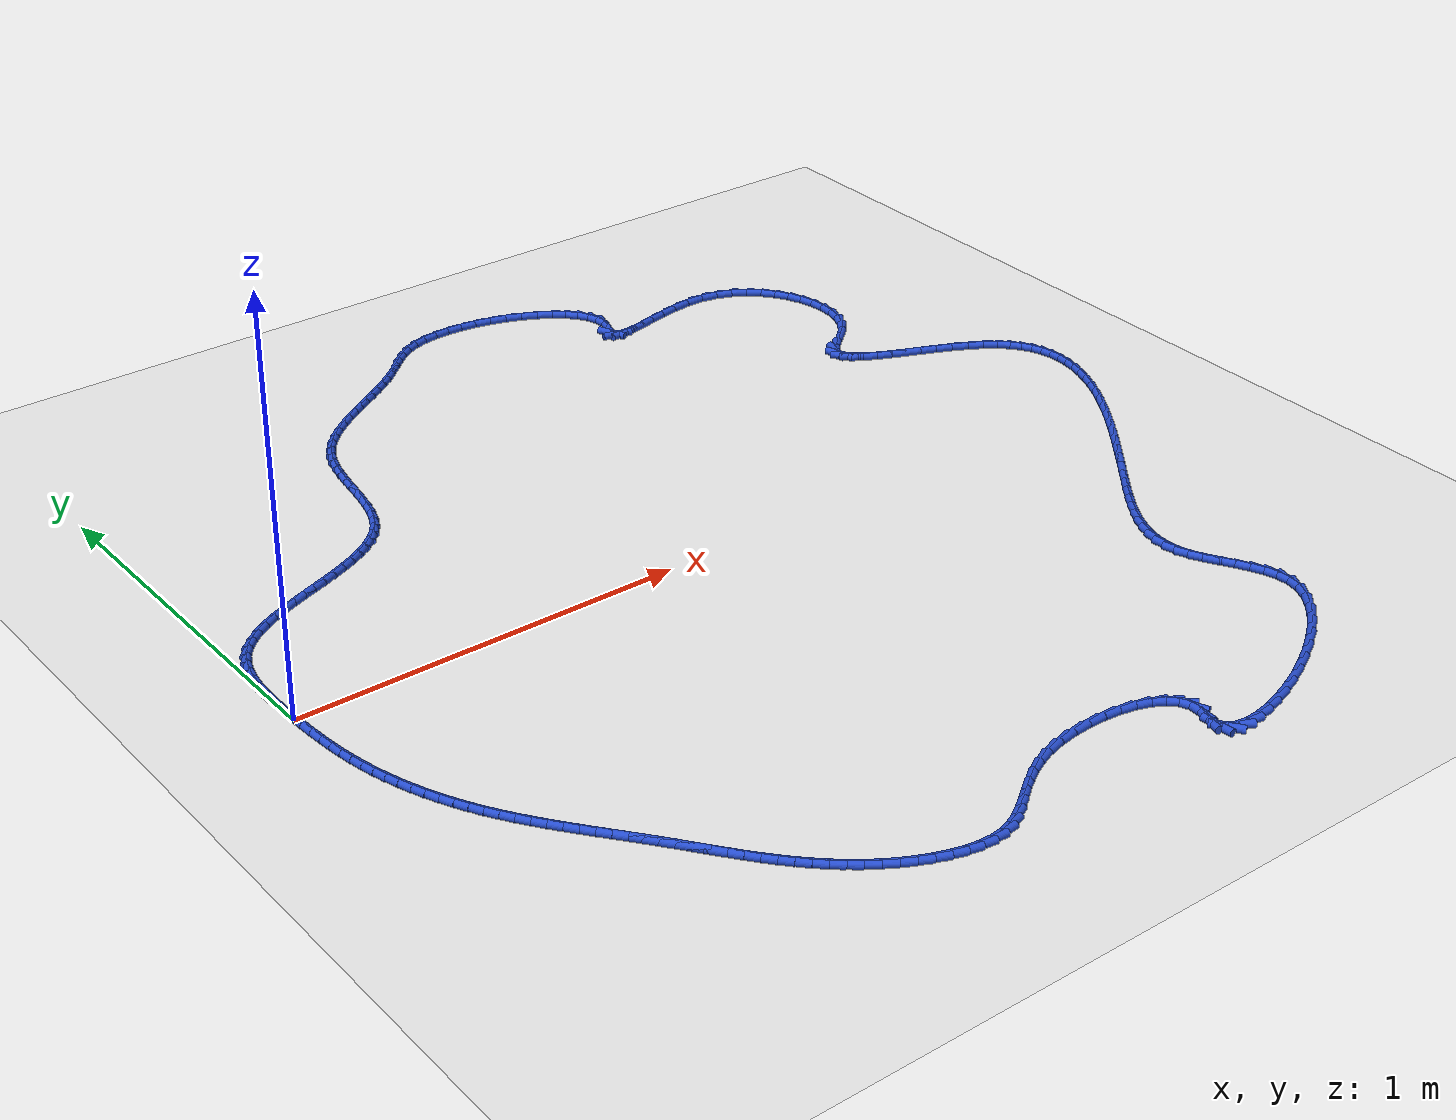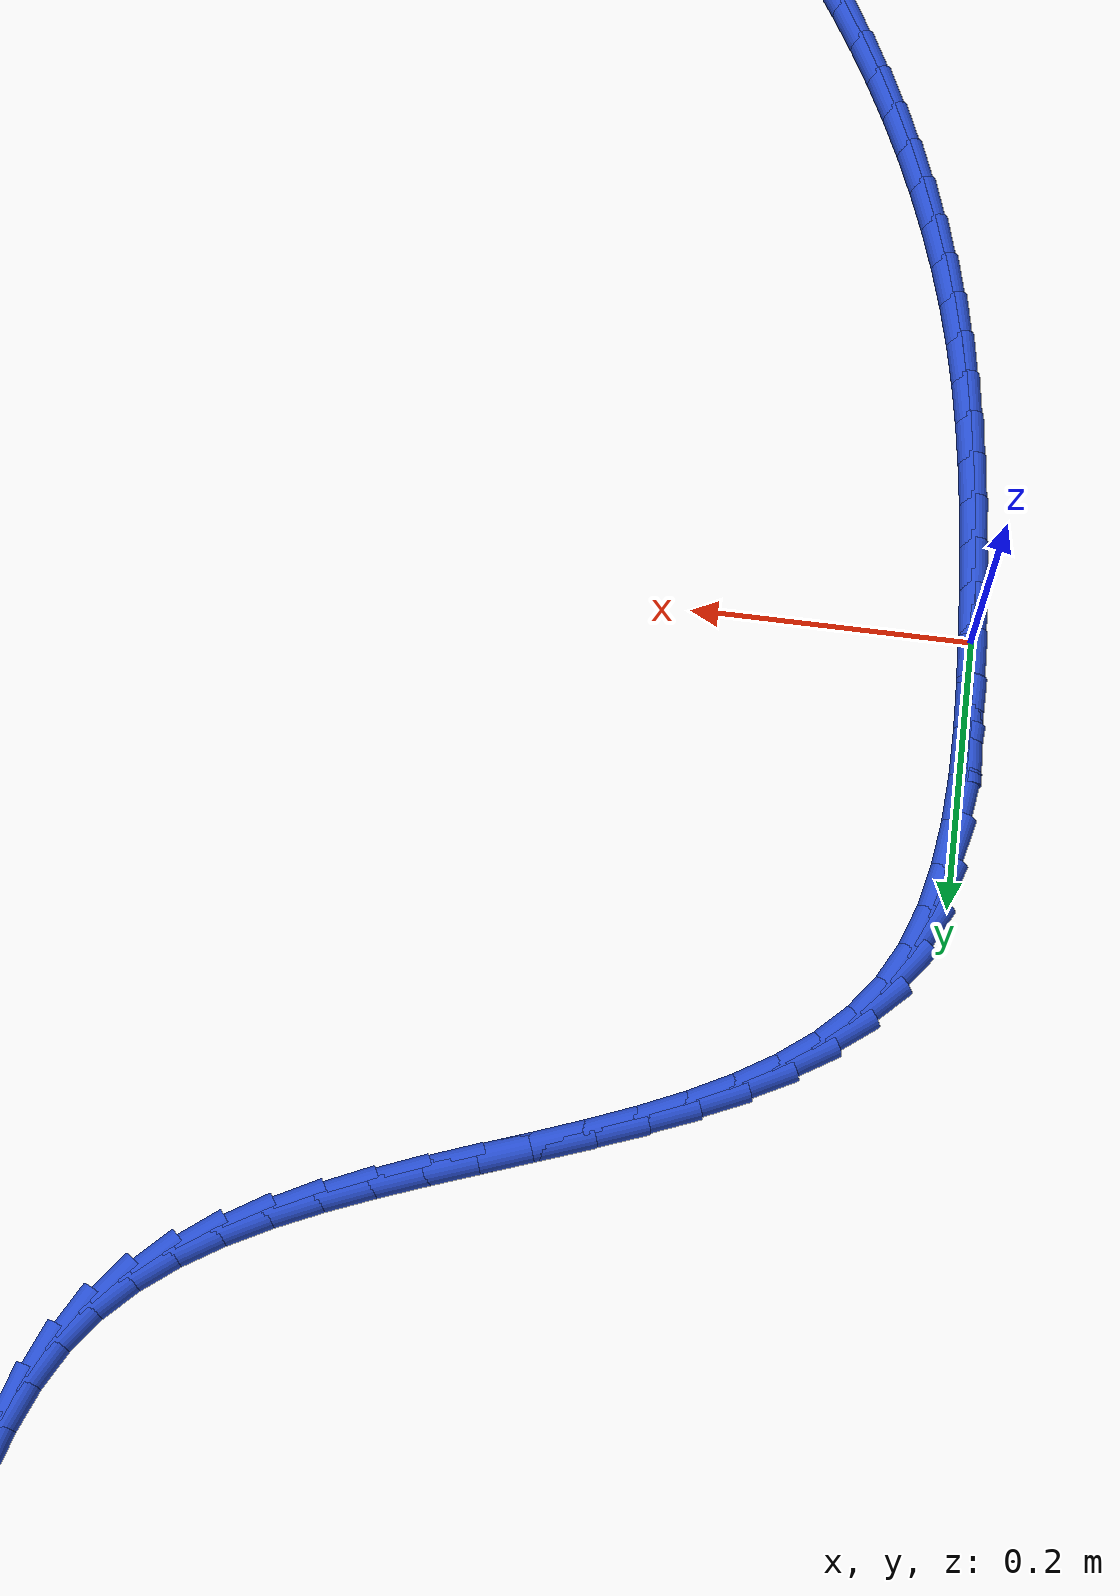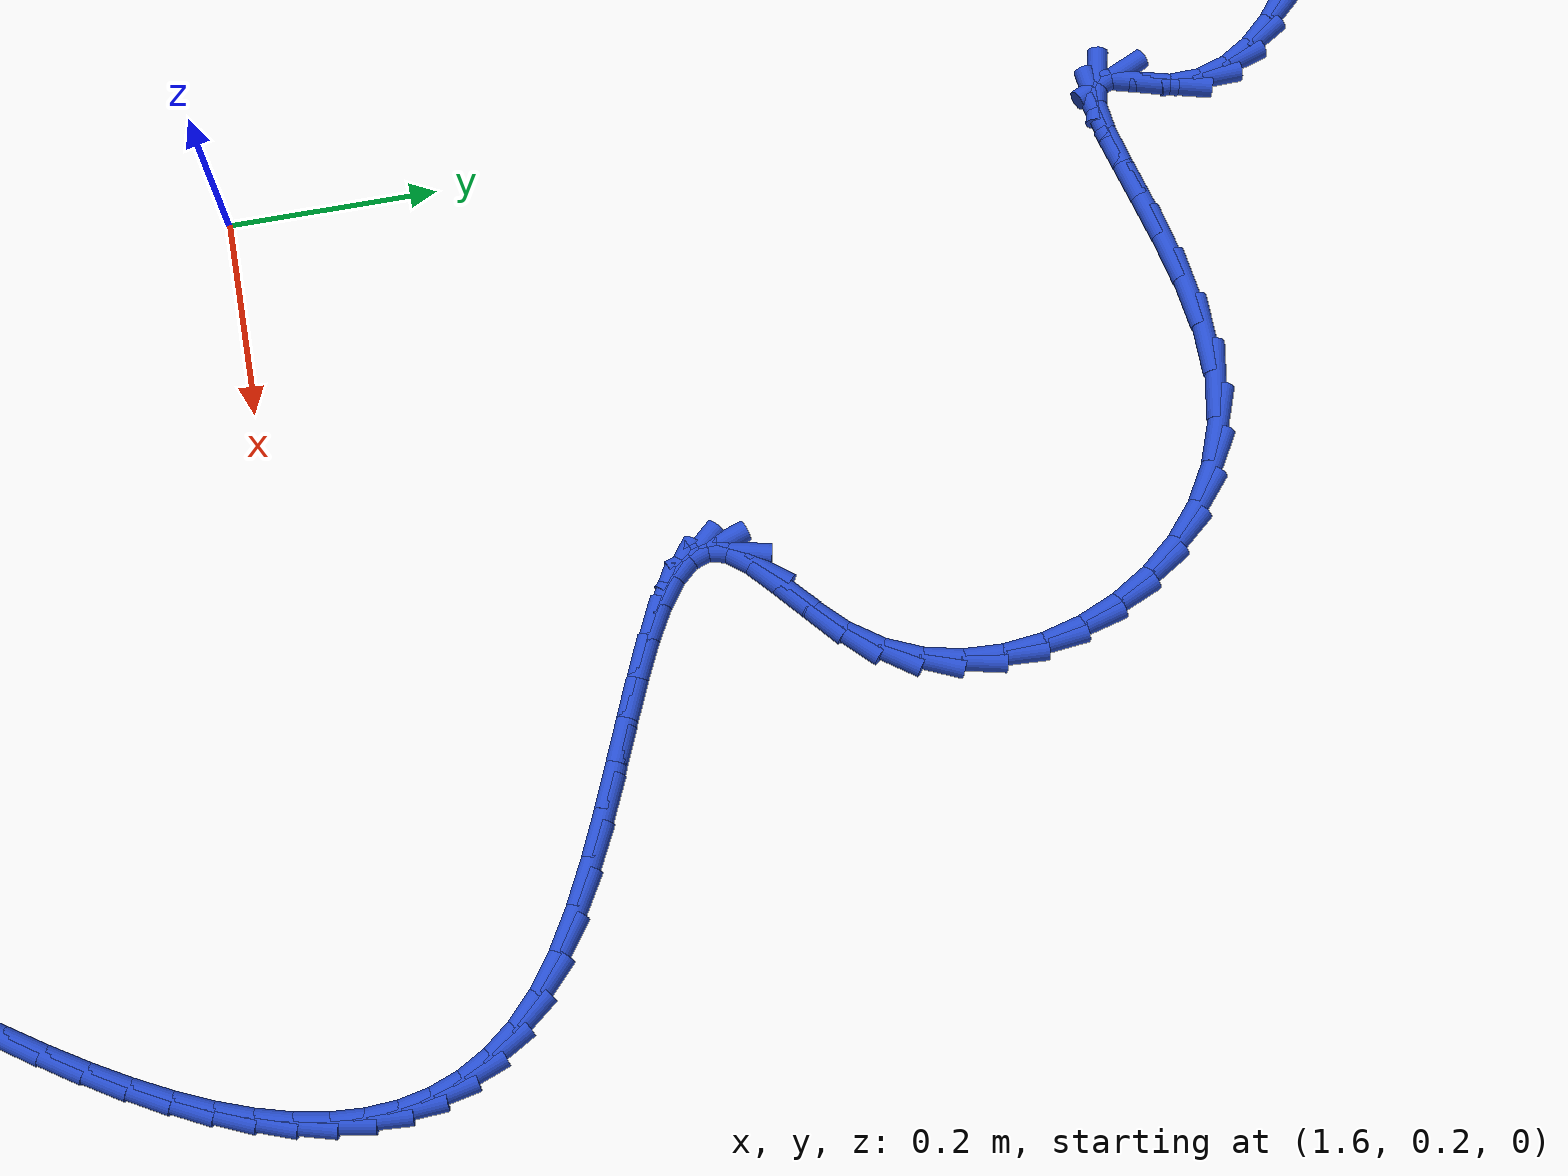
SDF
<sdf version="1.6">
 <world name="default">
  <light name="sun" type="directional">
   <pose>0 0 10 0 -0 0</pose>
   <diffuse>0.8 0.8 0.8 1</diffuse>
   <specular>0.2 0.2 0.2 1</specular>
   <attenuation>
    <range>1000</range>
    <constant>0.9</constant>
    <linear>0.01</linear>
    <quadratic>0.001</quadratic>
   </attenuation>
   <direction>-0.5 0.1 -0.9</direction>
  </light>
  <model name="ground_plane">
   <static>1</static>
   <link name="link">
    <collision name="collision">
     <geometry><plane><normal>0 0 1</normal><size>100 100</size></plane></geometry>
     <surface><friction><ode><mu>100</mu><mu2>50</mu2></ode></friction></surface>
    </collision>
    <visual name="visual">
     <cast_shadows>0</cast_shadows>
     <geometry><plane><normal>0 0 1</normal><size>100 100</size></plane></geometry>
     <material>
      <script><uri>file://media/materials/scripts/gazebo.material</uri><name>Gazebo/WhiteGlow</name></script>
     </material>
    </visual>
   </link>
  </model>
  <gravity>0 0 -9.8</gravity>
  <magnetic_field>6e-06 2.3e-05 -4.2e-05</magnetic_field>
  <atmosphere type="adiabatic"/>
  <physics name="default_physics" default="0" type="ode">
   <max_step_size>0.001</max_step_size>
   <real_time_factor>1</real_time_factor>
   <real_time_update_rate>1000</real_time_update_rate>
  </physics>
  <scene><ambient>0.4 0.4 0.4 1</ambient><background>0.7 0.7 0.7 1</background><shadows>1</shadows></scene>
  <spherical_coordinates>
   <surface_model>EARTH_WGS84</surface_model>
   <latitude_deg>0</latitude_deg>
   <longitude_deg>0</longitude_deg>
   <elevation>0</elevation>
   <heading_deg>0</heading_deg>
  </spherical_coordinates>
  <model name="line">
   <link name="link_0">
    <pose>-1.0408340855860843e-17 -6.245004513516506e-17 0.01 0 1.57 -1.5242962245123777</pose>
    <collision name="collision">
     <geometry><cylinder><radius>0.01</radius><length>0.08</length></cylinder></geometry>
    </collision>
    <visual name="visual">
     <material>
      <script><name>Gazebo/Blue</name><uri>file://media/materials/scripts/gazebo.material</uri></script>
     </material>
     <geometry><cylinder><radius>0.01</radius><length>0.08</length></cylinder></geometry>
    </visual>
   </link>
   <link name="link_1">
    <pose>-0.001641731145644832 0.03528051792536974 0.01 0 1.57 -1.5468645487586332</pose>
    <collision name="collision">
     <geometry><cylinder><radius>0.01</radius><length>0.08</length></cylinder></geometry>
    </collision>
    <visual name="visual">
     <material>
      <script><name>Gazebo/Blue</name><uri>file://media/materials/scripts/gazebo.material</uri></script>
     </material>
     <geometry><cylinder><radius>0.01</radius><length>0.08</length></cylinder></geometry>
    </visual>
   </link>
   <link name="link_2">
    <pose>-0.002492273666800602 0.07081403058766653 0.01 0 1.57 1.5585439790314888</pose>
    <collision name="collision">
     <geometry><cylinder><radius>0.01</radius><length>0.08</length></cylinder></geometry>
    </collision>
    <visual name="visual">
     <material>
      <script><name>Gazebo/Blue</name><uri>file://media/materials/scripts/gazebo.material</uri></script>
     </material>
     <geometry><cylinder><radius>0.01</radius><length>0.08</length></cylinder></geometry>
    </visual>
   </link>
   <link name="link_3">
    <pose>-0.0020595682603095273 0.10612838519522573 0.01 0 1.57 1.5071096498755654</pose>
    <collision name="collision">
     <geometry><cylinder><radius>0.01</radius><length>0.08</length></cylinder></geometry>
    </collision>
    <visual name="visual">
     <material>
      <script><name>Gazebo/Blue</name><uri>file://media/materials/scripts/gazebo.material</uri></script>
     </material>
     <geometry><cylinder><radius>0.01</radius><length>0.08</length></cylinder></geometry>
    </visual>
   </link>
   <link name="link_4">
    <pose>0.00014844437698618117 0.1407514289563828 0.01 0 1.57 1.4378307206908574</pose>
    <collision name="collision">
     <geometry><cylinder><radius>0.01</radius><length>0.08</length></cylinder></geometry>
    </collision>
    <visual name="visual">
     <material>
      <script><name>Gazebo/Blue</name><uri>file://media/materials/scripts/gazebo.material</uri></script>
     </material>
     <geometry><cylinder><radius>0.01</radius><length>0.08</length></cylinder></geometry>
    </visual>
   </link>
   <link name="link_5">
    <pose>0.004623823548244313 0.1742110090794732 0.01 0 1.57 1.3472573982862939</pose>
    <collision name="collision">
     <geometry><cylinder><radius>0.01</radius><length>0.08</length></cylinder></geometry>
    </collision>
    <visual name="visual">
     <material>
      <script><name>Gazebo/Blue</name><uri>file://media/materials/scripts/gazebo.material</uri></script>
     </material>
     <geometry><cylinder><radius>0.01</radius><length>0.08</length></cylinder></geometry>
    </visual>
   </link>
   <link name="link_6">
    <pose>0.011858628556622668 0.2060349727728325 0.01 0 1.57 1.2315569330320024</pose>
    <collision name="collision">
     <geometry><cylinder><radius>0.01</radius><length>0.08</length></cylinder></geometry>
    </collision>
    <visual name="visual">
     <material>
      <script><name>Gazebo/Blue</name><uri>file://media/materials/scripts/gazebo.material</uri></script>
     </material>
     <geometry><cylinder><radius>0.01</radius><length>0.08</length></cylinder></geometry>
    </visual>
   </link>
   <link name="link_7">
    <pose>0.022344918705279018 0.23575116724479603 0.01 0 1.57 1.0878575632266727</pose>
    <collision name="collision">
     <geometry><cylinder><radius>0.01</radius><length>0.08</length></cylinder></geometry>
    </collision>
    <visual name="visual">
     <material>
      <script><name>Gazebo/Blue</name><uri>file://media/materials/scripts/gazebo.material</uri></script>
     </material>
     <geometry><cylinder><radius>0.01</radius><length>0.08</length></cylinder></geometry>
    </visual>
   </link>
   <link name="link_8">
    <pose>0.03657414379491462 0.26288795534059767 0.01 0 1.57 0.9271885301556586</pose>
    <collision name="collision">
     <geometry><cylinder><radius>0.01</radius><length>0.08</length></cylinder></geometry>
    </collision>
    <visual name="visual">
     <material>
      <script><name>Gazebo/Blue</name><uri>file://media/materials/scripts/gazebo.material</uri></script>
     </material>
     <geometry><cylinder><radius>0.01</radius><length>0.08</length></cylinder></geometry>
    </visual>
   </link>
   <link name="link_9">
    <pose>0.05479593500196286 0.28717827759677617 0.01 0 1.57 0.7816756826921644</pose>
    <collision name="collision">
     <geometry><cylinder><radius>0.01</radius><length>0.08</length></cylinder></geometry>
    </collision>
    <visual name="visual">
     <material>
      <script><name>Gazebo/Blue</name><uri>file://media/materials/scripts/gazebo.material</uri></script>
     </material>
     <geometry><cylinder><radius>0.01</radius><length>0.08</length></cylinder></geometry>
    </visual>
   </link>
   <link name="link_10">
    <pose>0.07665044875000045 0.30887068801109635 0.01 0 1.57 0.6598725122205333</pose>
    <collision name="collision">
     <geometry><cylinder><radius>0.01</radius><length>0.08</length></cylinder></geometry>
    </collision>
    <visual name="visual">
     <material>
      <script><name>Gazebo/Blue</name><uri>file://media/materials/scripts/gazebo.material</uri></script>
     </material>
     <geometry><cylinder><radius>0.01</radius><length>0.08</length></cylinder></geometry>
    </visual>
   </link>
   <link name="link_11">
    <pose>0.10168331765974586 0.32829370738049224 0.01 0 1.57 0.5620662765005381</pose>
    <collision name="collision">
     <geometry><cylinder><radius>0.01</radius><length>0.08</length></cylinder></geometry>
    </collision>
    <visual name="visual">
     <material>
      <script><name>Gazebo/Blue</name><uri>file://media/materials/scripts/gazebo.material</uri></script>
     </material>
     <geometry><cylinder><radius>0.01</radius><length>0.08</length></cylinder></geometry>
    </visual>
   </link>
   <link name="link_12">
    <pose>0.1294401743519176 0.3457758565018975 0.01 0 1.57 0.4862077969593098</pose>
    <collision name="collision">
     <geometry><cylinder><radius>0.01</radius><length>0.08</length></cylinder></geometry>
    </collision>
    <visual name="visual">
     <material>
      <script><name>Gazebo/Blue</name><uri>file://media/materials/scripts/gazebo.material</uri></script>
     </material>
     <geometry><cylinder><radius>0.01</radius><length>0.08</length></cylinder></geometry>
    </visual>
   </link>
   <link name="link_13">
    <pose>0.1594666514472341 0.36164565617224603 0.01 0 1.57 0.4295506016939071</pose>
    <collision name="collision">
     <geometry><cylinder><radius>0.01</radius><length>0.08</length></cylinder></geometry>
    </collision>
    <visual name="visual">
     <material>
      <script><name>Gazebo/Blue</name><uri>file://media/materials/scripts/gazebo.material</uri></script>
     </material>
     <geometry><cylinder><radius>0.01</radius><length>0.08</length></cylinder></geometry>
    </visual>
   </link>
   <link name="link_14">
    <pose>0.19130838156641392 0.37623162718847164 0.01 0 1.57 0.389550702468506</pose>
    <collision name="collision">
     <geometry><cylinder><radius>0.01</radius><length>0.08</length></cylinder></geometry>
    </collision>
    <visual name="visual">
     <material>
      <script><name>Gazebo/Blue</name><uri>file://media/materials/scripts/gazebo.material</uri></script>
     </material>
     <geometry><cylinder><radius>0.01</radius><length>0.08</length></cylinder></geometry>
    </visual>
   </link>
   <link name="link_15">
    <pose>0.2245109973301755 0.38986229034750813 0.01 0 1.57 0.3642329124297852</pose>
    <collision name="collision">
     <geometry><cylinder><radius>0.01</radius><length>0.08</length></cylinder></geometry>
    </collision>
    <visual name="visual">
     <material>
      <script><name>Gazebo/Blue</name><uri>file://media/materials/scripts/gazebo.material</uri></script>
     </material>
     <geometry><cylinder><radius>0.01</radius><length>0.08</length></cylinder></geometry>
    </visual>
   </link>
   <link name="link_16">
    <pose>0.2586201313592373 0.4028661664462892 0.01 0 1.57 0.35228973752327797</pose>
    <collision name="collision">
     <geometry><cylinder><radius>0.01</radius><length>0.08</length></cylinder></geometry>
    </collision>
    <visual name="visual">
     <material>
      <script><name>Gazebo/Blue</name><uri>file://media/materials/scripts/gazebo.material</uri></script>
     </material>
     <geometry><cylinder><radius>0.01</radius><length>0.08</length></cylinder></geometry>
    </visual>
   </link>
   <link name="link_17">
    <pose>0.2931814162743178 0.41557177628174874 0.01 0 1.57 0.3530814933342306</pose>
    <collision name="collision">
     <geometry><cylinder><radius>0.01</radius><length>0.08</length></cylinder></geometry>
    </collision>
    <visual name="visual">
     <material>
      <script><name>Gazebo/Blue</name><uri>file://media/materials/scripts/gazebo.material</uri></script>
     </material>
     <geometry><cylinder><radius>0.01</radius><length>0.08</length></cylinder></geometry>
    </visual>
   </link>
   <link name="link_18">
    <pose>0.3277404846961356 0.42830764065082055 0.01 0 1.57 0.36661938496942403</pose>
    <collision name="collision">
     <geometry><cylinder><radius>0.01</radius><length>0.08</length></cylinder></geometry>
    </collision>
    <visual name="visual">
     <material>
      <script><name>Gazebo/Blue</name><uri>file://media/materials/scripts/gazebo.material</uri></script>
     </material>
     <geometry><cylinder><radius>0.01</radius><length>0.08</length></cylinder></geometry>
    </visual>
   </link>
   <link name="link_19">
    <pose>0.36184296924540893 0.44140228035043844 0.01 0 1.57 0.3935616112670279</pose>
    <collision name="collision">
     <geometry><cylinder><radius>0.01</radius><length>0.08</length></cylinder></geometry>
    </collision>
    <visual name="visual">
     <material>
      <script><name>Gazebo/Blue</name><uri>file://media/materials/scripts/gazebo.material</uri></script>
     </material>
     <geometry><cylinder><radius>0.01</radius><length>0.08</length></cylinder></geometry>
    </visual>
   </link>
   <link name="link_20">
    <pose>0.39503450254285655 0.4551842161775361 0.01 0 1.57 0.43522054618761513</pose>
    <collision name="collision">
     <geometry><cylinder><radius>0.01</radius><length>0.08</length></cylinder></geometry>
    </collision>
    <visual name="visual">
     <material>
      <script><name>Gazebo/Blue</name><uri>file://media/materials/scripts/gazebo.material</uri></script>
     </material>
     <geometry><cylinder><radius>0.01</radius><length>0.08</length></cylinder></geometry>
    </visual>
   </link>
   <link name="link_21">
    <pose>0.4268607172091969 0.46998196892904753 0.01 0 1.57 0.4935467505105887</pose>
    <collision name="collision">
     <geometry><cylinder><radius>0.01</radius><length>0.08</length></cylinder></geometry>
    </collision>
    <visual name="visual">
     <material>
      <script><name>Gazebo/Blue</name><uri>file://media/materials/scripts/gazebo.material</uri></script>
     </material>
     <geometry><cylinder><radius>0.01</radius><length>0.08</length></cylinder></geometry>
    </visual>
   </link>
   <link name="link_22">
    <pose>0.4568672458651484 0.4861240594019064 0.01 0 1.57 0.5710039123562387</pose>
    <collision name="collision">
     <geometry><cylinder><radius>0.01</radius><length>0.08</length></cylinder></geometry>
    </collision>
    <visual name="visual">
     <material>
      <script><name>Gazebo/Blue</name><uri>file://media/materials/scripts/gazebo.material</uri></script>
     </material>
     <geometry><cylinder><radius>0.01</radius><length>0.08</length></cylinder></geometry>
    </visual>
   </link>
   <link name="link_23">
    <pose>0.48459972113142963 0.5039390083930466 0.01 0 1.57 0.6701661214677855</pose>
    <collision name="collision">
     <geometry><cylinder><radius>0.01</radius><length>0.08</length></cylinder></geometry>
    </collision>
    <visual name="visual">
     <material>
      <script><name>Gazebo/Blue</name><uri>file://media/materials/scripts/gazebo.material</uri></script>
     </material>
     <geometry><cylinder><radius>0.01</radius><length>0.08</length></cylinder></geometry>
    </visual>
   </link>
   <link name="link_24">
    <pose>0.5096037756287588 0.5237553366994018 0.01 0 1.57 0.7927889905109694</pose>
    <collision name="collision">
     <geometry><cylinder><radius>0.01</radius><length>0.08</length></cylinder></geometry>
    </collision>
    <visual name="visual">
     <material>
      <script><name>Gazebo/Blue</name><uri>file://media/materials/scripts/gazebo.material</uri></script>
     </material>
     <geometry><cylinder><radius>0.01</radius><length>0.08</length></cylinder></geometry>
    </visual>
   </link>
   <link name="link_25">
    <pose>0.5314250419778546 0.5459015651179057 0.01 0 1.57 0.9379550338414256</pose>
    <collision name="collision">
     <geometry><cylinder><radius>0.01</radius><length>0.08</length></cylinder></geometry>
    </collision>
    <visual name="visual">
     <material>
      <script><name>Gazebo/Blue</name><uri>file://media/materials/scripts/gazebo.material</uri></script>
     </material>
     <geometry><cylinder><radius>0.01</radius><length>0.08</length></cylinder></geometry>
    </visual>
   </link>
   <link name="link_26">
    <pose>0.5496154136914476 0.5707018088195751 0.01 0 1.57 1.0852024332402437</pose>
    <collision name="collision">
     <geometry><cylinder><radius>0.01</radius><length>0.08</length></cylinder></geometry>
    </collision>
    <visual name="visual">
     <material>
      <script><name>Gazebo/Blue</name><uri>file://media/materials/scripts/gazebo.material</uri></script>
     </material>
     <geometry><cylinder><radius>0.01</radius><length>0.08</length></cylinder></geometry>
    </visual>
   </link>
   <link name="link_27">
    <pose>0.5641267064366456 0.5981987682177582 0.01 0 1.57 1.2047762585858934</pose>
    <collision name="collision">
     <geometry><cylinder><radius>0.01</radius><length>0.08</length></cylinder></geometry>
    </collision>
    <visual name="visual">
     <material>
      <script><name>Gazebo/Blue</name><uri>file://media/materials/scripts/gazebo.material</uri></script>
     </material>
     <geometry><cylinder><radius>0.01</radius><length>0.08</length></cylinder></geometry>
    </visual>
   </link>
   <link name="link_28">
    <pose>0.5755449876322221 0.6279888373608263 0.01 0 1.57 1.2946129401444089</pose>
    <collision name="collision">
     <geometry><cylinder><radius>0.01</radius><length>0.08</length></cylinder></geometry>
    </collision>
    <visual name="visual">
     <material>
      <script><name>Gazebo/Blue</name><uri>file://media/materials/scripts/gazebo.material</uri></script>
     </material>
     <geometry><cylinder><radius>0.01</radius><length>0.08</length></cylinder></geometry>
    </visual>
   </link>
   <link name="link_29">
    <pose>0.5845125990711096 0.6596288114922465 0.01 0 1.57 1.3574516544420843</pose>
    <collision name="collision">
     <geometry><cylinder><radius>0.01</radius><length>0.08</length></cylinder></geometry>
    </collision>
    <visual name="visual">
     <material>
      <script><name>Gazebo/Blue</name><uri>file://media/materials/scripts/gazebo.material</uri></script>
     </material>
     <geometry><cylinder><radius>0.01</radius><length>0.08</length></cylinder></geometry>
    </visual>
   </link>
   <link name="link_30">
    <pose>0.5916718825462428 0.6926754858554875 0.01 0 1.57 1.3963664404026424</pose>
    <collision name="collision">
     <geometry><cylinder><radius>0.01</radius><length>0.08</length></cylinder></geometry>
    </collision>
    <visual name="visual">
     <material>
      <script><name>Gazebo/Blue</name><uri>file://media/materials/scripts/gazebo.material</uri></script>
     </material>
     <geometry><cylinder><radius>0.01</radius><length>0.08</length></cylinder></geometry>
    </visual>
   </link>
   <link name="link_31">
    <pose>0.5976651798505553 0.7266856556940167 0.01 0 1.57 1.4137007249482834</pose>
    <collision name="collision">
     <geometry><cylinder><radius>0.01</radius><length>0.08</length></cylinder></geometry>
    </collision>
    <visual name="visual">
     <material>
      <script><name>Gazebo/Blue</name><uri>file://media/materials/scripts/gazebo.material</uri></script>
     </material>
     <geometry><cylinder><radius>0.01</radius><length>0.08</length></cylinder></geometry>
    </visual>
   </link>
   <link name="link_32">
    <pose>0.6031348327769809 0.7612161162513018 0.01 0 1.57 1.4107004888592813</pose>
    <collision name="collision">
     <geometry><cylinder><radius>0.01</radius><length>0.08</length></cylinder></geometry>
    </collision>
    <visual name="visual">
     <material>
      <script><name>Gazebo/Blue</name><uri>file://media/materials/scripts/gazebo.material</uri></script>
     </material>
     <geometry><cylinder><radius>0.01</radius><length>0.08</length></cylinder></geometry>
    </visual>
   </link>
   <link name="link_33">
    <pose>0.6087231831184532 0.795823662770811 0.01 0 1.57 1.3874487769452046</pose>
    <collision name="collision">
     <geometry><cylinder><radius>0.01</radius><length>0.08</length></cylinder></geometry>
    </collision>
    <visual name="visual">
     <material>
      <script><name>Gazebo/Blue</name><uri>file://media/materials/scripts/gazebo.material</uri></script>
     </material>
     <geometry><cylinder><radius>0.01</radius><length>0.08</length></cylinder></geometry>
    </visual>
   </link>
   <link name="link_34">
    <pose>0.6150725726679064 0.8300650904960117 0.01 0 1.57 1.3429279647191183</pose>
    <collision name="collision">
     <geometry><cylinder><radius>0.01</radius><length>0.08</length></cylinder></geometry>
    </collision>
    <visual name="visual">
     <material>
      <script><name>Gazebo/Blue</name><uri>file://media/materials/scripts/gazebo.material</uri></script>
     </material>
     <geometry><cylinder><radius>0.01</radius><length>0.08</length></cylinder></geometry>
    </visual>
   </link>
   <link name="link_35">
    <pose>0.6228253432182742 0.8634971946703722 0.01 0 1.57 1.2752215546825723</pose>
    <collision name="collision">
     <geometry><cylinder><radius>0.01</radius><length>0.08</length></cylinder></geometry>
    </collision>
    <visual name="visual">
     <material>
      <script><name>Gazebo/Blue</name><uri>file://media/materials/scripts/gazebo.material</uri></script>
     </material>
     <geometry><cylinder><radius>0.01</radius><length>0.08</length></cylinder></geometry>
    </visual>
   </link>
   <link name="link_36">
    <pose>0.6326238365624903 0.8956767705373601 0.01 0 1.57 1.182031020234204</pose>
    <collision name="collision">
     <geometry><cylinder><radius>0.01</radius><length>0.08</length></cylinder></geometry>
    </collision>
    <visual name="visual">
     <material>
      <script><name>Gazebo/Blue</name><uri>file://media/materials/scripts/gazebo.material</uri></script>
     </material>
     <geometry><cylinder><radius>0.01</radius><length>0.08</length></cylinder></geometry>
    </visual>
   </link>
   <link name="link_37">
    <pose>0.6451103944934886 0.9261606133404434 0.01 0 1.57 1.0628653737954108</pose>
    <collision name="collision">
     <geometry><cylinder><radius>0.01</radius><length>0.08</length></cylinder></geometry>
    </collision>
    <visual name="visual">
     <material>
      <script><name>Gazebo/Blue</name><uri>file://media/materials/scripts/gazebo.material</uri></script>
     </material>
     <geometry><cylinder><radius>0.01</radius><length>0.08</length></cylinder></geometry>
    </visual>
   </link>
   <link name="link_38">
    <pose>0.6608985629883449 0.9545236743563121 0.01 0 1.57 0.9394329332841489</pose>
    <collision name="collision">
     <geometry><cylinder><radius>0.01</radius><length>0.08</length></cylinder></geometry>
    </collision>
    <visual name="visual">
     <material>
      <script><name>Gazebo/Blue</name><uri>file://media/materials/scripts/gazebo.material</uri></script>
     </material>
     <geometry><cylinder><radius>0.01</radius><length>0.08</length></cylinder></geometry>
    </visual>
   </link>
   <link name="link_39">
    <pose>0.680036782411011 0.980697209275339 0.01 0 1.57 0.8333425290194094</pose>
    <collision name="collision">
     <geometry><cylinder><radius>0.01</radius><length>0.08</length></cylinder></geometry>
    </collision>
    <visual name="visual">
     <material>
      <script><name>Gazebo/Blue</name><uri>file://media/materials/scripts/gazebo.material</uri></script>
     </material>
     <geometry><cylinder><radius>0.01</radius><length>0.08</length></cylinder></geometry>
    </visual>
   </link>
   <link name="link_40">
    <pose>0.702057630298072 1.004937730161178 0.01 0 1.57 0.7462383159895453</pose>
    <collision name="collision">
     <geometry><cylinder><radius>0.01</radius><length>0.08</length></cylinder></geometry>
    </collision>
    <visual name="visual">
     <material>
      <script><name>Gazebo/Blue</name><uri>file://media/materials/scripts/gazebo.material</uri></script>
     </material>
     <geometry><cylinder><radius>0.01</radius><length>0.08</length></cylinder></geometry>
    </visual>
   </link>
   <link name="link_41">
    <pose>0.7264747625972505 1.0275136793175477 0.01 0 1.57 0.6774716742403745</pose>
    <collision name="collision">
     <geometry><cylinder><radius>0.01</radius><length>0.08</length></cylinder></geometry>
    </collision>
    <visual name="visual">
     <material>
      <script><name>Gazebo/Blue</name><uri>file://media/materials/scripts/gazebo.material</uri></script>
     </material>
     <geometry><cylinder><radius>0.01</radius><length>0.08</length></cylinder></geometry>
    </visual>
   </link>
   <link name="link_42">
    <pose>0.7528018352562678 1.0486934990481662 0.01 0 1.57 0.6257214159362816</pose>
    <collision name="collision">
     <geometry><cylinder><radius>0.01</radius><length>0.08</length></cylinder></geometry>
    </collision>
    <visual name="visual">
     <material>
      <script><name>Gazebo/Blue</name><uri>file://media/materials/scripts/gazebo.material</uri></script>
     </material>
     <geometry><cylinder><radius>0.01</radius><length>0.08</length></cylinder></geometry>
    </visual>
   </link>
   <link name="link_43">
    <pose>0.7805525042228462 1.0687456316567514 0.01 0 1.57 0.5896323464035661</pose>
    <collision name="collision">
     <geometry><cylinder><radius>0.01</radius><length>0.08</length></cylinder></geometry>
    </collision>
    <visual name="visual">
     <material>
      <script><name>Gazebo/Blue</name><uri>file://media/materials/scripts/gazebo.material</uri></script>
     </material>
     <geometry><cylinder><radius>0.01</radius><length>0.08</length></cylinder></geometry>
    </visual>
   </link>
   <link name="link_44">
    <pose>0.8092404254447071 1.087938519447021 0.01 0 1.57 0.5681737955948196</pose>
    <collision name="collision">
     <geometry><cylinder><radius>0.01</radius><length>0.08</length></cylinder></geometry>
    </collision>
    <visual name="visual">
     <material>
      <script><name>Gazebo/Blue</name><uri>file://media/materials/scripts/gazebo.material</uri></script>
     </material>
     <geometry><cylinder><radius>0.01</radius><length>0.08</length></cylinder></geometry>
    </visual>
   </link>
   <link name="link_45">
    <pose>0.8383792548695731 1.1065406047226938 0.01 0 1.57 0.5608223122984245</pose>
    <collision name="collision">
     <geometry><cylinder><radius>0.01</radius><length>0.08</length></cylinder></geometry>
    </collision>
    <visual name="visual">
     <material>
      <script><name>Gazebo/Blue</name><uri>file://media/materials/scripts/gazebo.material</uri></script>
     </material>
     <geometry><cylinder><radius>0.01</radius><length>0.08</length></cylinder></geometry>
    </visual>
   </link>
   <link name="link_46">
    <pose>0.8674826638000634 1.124820329600047 0.01 0 1.57 0.5664427880120331</pose>
    <collision name="collision">
     <geometry><cylinder><radius>0.01</radius><length>0.08</length></cylinder></geometry>
    </collision>
    <visual name="visual">
     <material>
      <script><name>Gazebo/Blue</name><uri>file://media/materials/scripts/gazebo.material</uri></script>
     </material>
     <geometry><cylinder><radius>0.01</radius><length>0.08</length></cylinder></geometry>
    </visual>
   </link>
   <link name="link_47">
    <pose>0.8961398863788326 1.1430452137835292 0.01 0 1.57 0.5814035614070694</pose>
    <collision name="collision">
     <geometry><cylinder><radius>0.01</radius><length>0.08</length></cylinder></geometry>
    </collision>
    <visual name="visual">
     <material>
      <script><name>Gazebo/Blue</name><uri>file://media/materials/scripts/gazebo.material</uri></script>
     </material>
     <geometry><cylinder><radius>0.01</radius><length>0.08</length></cylinder></geometry>
    </visual>
   </link>
   <link name="link_48">
    <pose>0.9241909599313513 1.1614797153692287 0.01 0 1.57 0.6051087265047465</pose>
    <collision name="collision">
     <geometry><cylinder><radius>0.01</radius><length>0.08</length></cylinder></geometry>
    </collision>
    <visual name="visual">
     <material>
      <script><name>Gazebo/Blue</name><uri>file://media/materials/scripts/gazebo.material</uri></script>
     </material>
     <geometry><cylinder><radius>0.01</radius><length>0.08</length></cylinder></geometry>
    </visual>
   </link>
   <link name="link_49">
    <pose>0.9515278891134051 1.180387658076864 0.01 0 1.57 0.6376613649610068</pose>
    <collision name="collision">
     <geometry><cylinder><radius>0.01</radius><length>0.08</length></cylinder></geometry>
    </collision>
    <visual name="visual">
     <material>
      <script><name>Gazebo/Blue</name><uri>file://media/materials/scripts/gazebo.material</uri></script>
     </material>
     <geometry><cylinder><radius>0.01</radius><length>0.08</length></cylinder></geometry>
    </visual>
   </link>
   <link name="link_50">
    <pose>0.9780426785807792 1.2000328656261534 0.01 0 1.57 0.678982375466499</pose>
    <collision name="collision">
     <geometry><cylinder><radius>0.01</radius><length>0.08</length></cylinder></geometry>
    </collision>
    <visual name="visual">
     <material>
      <script><name>Gazebo/Blue</name><uri>file://media/materials/scripts/gazebo.material</uri></script>
     </material>
     <geometry><cylinder><radius>0.01</radius><length>0.08</length></cylinder></geometry>
    </visual>
   </link>
   <link name="link_51">
    <pose>1.0036273329892578 1.2206791617368147 0.01 0 1.57 0.724320663329092</pose>
    <collision name="collision">
     <geometry><cylinder><radius>0.01</radius><length>0.08</length></cylinder></geometry>
    </collision>
    <visual name="visual">
     <material>
      <script><name>Gazebo/Blue</name><uri>file://media/materials/scripts/gazebo.material</uri></script>
     </material>
     <geometry><cylinder><radius>0.01</radius><length>0.08</length></cylinder></geometry>
    </visual>
   </link>
   <link name="link_52">
    <pose>1.0282662865121477 1.242478262780542 0.01 0 1.57 0.7353628677841164</pose>
    <collision name="collision">
     <geometry><cylinder><radius>0.01</radius><length>0.08</length></cylinder></geometry>
    </collision>
    <visual name="visual">
     <material>
      <script><name>Gazebo/Blue</name><uri>file://media/materials/scripts/gazebo.material</uri></script>
     </material>
     <geometry><cylinder><radius>0.01</radius><length>0.08</length></cylinder></geometry>
    </visual>
   </link>
   <link name="link_53">
    <pose>1.0527393690378004 1.2646171532269688 0.01 0 1.57 0.6931060324528824</pose>
    <collision name="collision">
     <geometry><cylinder><radius>0.01</radius><length>0.08</length></cylinder></geometry>
    </collision>
    <visual name="visual">
     <material>
      <script><name>Gazebo/Blue</name><uri>file://media/materials/scripts/gazebo.material</uri></script>
     </material>
     <geometry><cylinder><radius>0.01</radius><length>0.08</length></cylinder></geometry>
    </visual>
   </link>
   <link name="link_54">
    <pose>1.0782321359848495 1.2857907148663508 0.01 0 1.57 0.598713805281445</pose>
    <collision name="collision">
     <geometry><cylinder><radius>0.01</radius><length>0.08</length></cylinder></geometry>
    </collision>
    <visual name="visual">
     <material>
      <script><name>Gazebo/Blue</name><uri>file://media/materials/scripts/gazebo.material</uri></script>
     </material>
     <geometry><cylinder><radius>0.01</radius><length>0.08</length></cylinder></geometry>
    </visual>
   </link>
   <link name="link_55">
    <pose>1.1059333835745753 1.3046898987339175 0.01 0 1.57 0.4576228024317589</pose>
    <collision name="collision">
     <geometry><cylinder><radius>0.01</radius><length>0.08</length></cylinder></geometry>
    </collision>
    <visual name="visual">
     <material>
      <script><name>Gazebo/Blue</name><uri>file://media/materials/scripts/gazebo.material</uri></script>
     </material>
     <geometry><cylinder><radius>0.01</radius><length>0.08</length></cylinder></geometry>
    </visual>
   </link>
   <link name="link_56">
    <pose>1.137031906055083 1.3200056573249026 0.01 0 1.57 0.2942016544670733</pose>
    <collision name="collision">
     <geometry><cylinder><radius>0.01</radius><length>0.08</length></cylinder></geometry>
    </collision>
    <visual name="visual">
     <material>
      <script><name>Gazebo/Blue</name><uri>file://media/materials/scripts/gazebo.material</uri></script>
     </material>
     <geometry><cylinder><radius>0.01</radius><length>0.08</length></cylinder></geometry>
    </visual>
   </link>
   <link name="link_57">
    <pose>1.1723435590150244 1.3307048893899986 0.01 0 1.57 0.15534807357436317</pose>
    <collision name="collision">
     <geometry><cylinder><radius>0.01</radius><length>0.08</length></cylinder></geometry>
    </collision>
    <visual name="visual">
     <material>
      <script><name>Gazebo/Blue</name><uri>file://media/materials/scripts/gazebo.material</uri></script>
     </material>
     <geometry><cylinder><radius>0.01</radius><length>0.08</length></cylinder></geometry>
    </visual>
   </link>
   <link name="link_58">
    <pose>1.2112697057273034 1.3368011104572703 0.01 0 1.57 0.042151408269883624</pose>
    <collision name="collision">
     <geometry><cylinder><radius>0.01</radius><length>0.08</length></cylinder></geometry>
    </collision>
    <visual name="visual">
     <material>
      <script><name>Gazebo/Blue</name><uri>file://media/materials/scripts/gazebo.material</uri></script>
     </material>
     <geometry><cylinder><radius>0.01</radius><length>0.08</length></cylinder></geometry>
    </visual>
   </link>
   <link name="link_59">
    <pose>1.2528764114338462 1.338555931106789 0.01 0 1.57 -0.05357706445981691</pose>
    <collision name="collision">
     <geometry><cylinder><radius>0.01</radius><length>0.08</length></cylinder></geometry>
    </collision>
    <visual name="visual">
     <material>
      <script><name>Gazebo/Blue</name><uri>file://media/materials/scripts/gazebo.material</uri></script>
     </material>
     <geometry><cylinder><radius>0.01</radius><length>0.08</length></cylinder></geometry>
    </visual>
   </link>
   <link name="link_60">
    <pose>1.2962297413765793 1.3362309619186254 0.01 0 1.57 -0.1382054735538119</pose>
    <collision name="collision">
     <geometry><cylinder><radius>0.01</radius><length>0.08</length></cylinder></geometry>
    </collision>
    <visual name="visual">
     <material>
      <script><name>Gazebo/Blue</name><uri>file://media/materials/scripts/gazebo.material</uri></script>
     </material>
     <geometry><cylinder><radius>0.01</radius><length>0.08</length></cylinder></geometry>
    </visual>
   </link>
   <link name="link_61">
    <pose>1.340395760797428 1.3300878134728509 0.01 0 1.57 -0.2167639707922253</pose>
    <collision name="collision">
     <geometry><cylinder><radius>0.01</radius><length>0.08</length></cylinder></geometry>
    </collision>
    <visual name="visual">
     <material>
      <script><name>Gazebo/Blue</name><uri>file://media/materials/scripts/gazebo.material</uri></script>
     </material>
     <geometry><cylinder><radius>0.01</radius><length>0.08</length></cylinder></geometry>
    </visual>
   </link>
   <link name="link_62">
    <pose>1.3844405349383193 1.3203880963495367 0.01 0 1.57 -0.2935425489364609</pose>
    <collision name="collision">
     <geometry><cylinder><radius>0.01</radius><length>0.08</length></cylinder></geometry>
    </collision>
    <visual name="visual">
     <material>
      <script><name>Gazebo/Blue</name><uri>file://media/materials/scripts/gazebo.material</uri></script>
     </material>
     <geometry><cylinder><radius>0.01</radius><length>0.08</length></cylinder></geometry>
    </visual>
   </link>
   <link name="link_63">
    <pose>1.4274301290411797 1.3073934211287537 0.01 0 1.57 -0.3726568076662822</pose>
    <collision name="collision">
     <geometry><cylinder><radius>0.01</radius><length>0.08</length></cylinder></geometry>
    </collision>
    <visual name="visual">
     <material>
      <script><name>Gazebo/Blue</name><uri>file://media/materials/scripts/gazebo.material</uri></script>
     </material>
     <geometry><cylinder><radius>0.01</radius><length>0.08</length></cylinder></geometry>
    </visual>
   </link>
   <link name="link_64">
    <pose>1.4684306083479337 1.2913653983905737 0.01 0 1.57 -0.4586146114452032</pose>
    <collision name="collision">
     <geometry><cylinder><radius>0.01</radius><length>0.08</length></cylinder></geometry>
    </collision>
    <visual name="visual">
     <material>
      <script><name>Gazebo/Blue</name><uri>file://media/materials/scripts/gazebo.material</uri></script>
     </material>
     <geometry><cylinder><radius>0.01</radius><length>0.08</length></cylinder></geometry>
    </visual>
   </link>
   <link name="link_65">
    <pose>1.5065080381005085 1.2725656387150677 0.01 0 1.57 -0.5569608270661742</pose>
    <collision name="collision">
     <geometry><cylinder><radius>0.01</radius><length>0.08</length></cylinder></geometry>
    </collision>
    <visual name="visual">
     <material>
      <script><name>Gazebo/Blue</name><uri>file://media/materials/scripts/gazebo.material</uri></script>
     </material>
     <geometry><cylinder><radius>0.01</radius><length>0.08</length></cylinder></geometry>
    </visual>
   </link>
   <link name="link_66">
    <pose>1.5407284835408315 1.251255752682307 0.01 0 1.57 -0.6750471116993496</pose>
    <collision name="collision">
     <geometry><cylinder><radius>0.01</radius><length>0.08</length></cylinder></geometry>
    </collision>
    <visual name="visual">
     <material>
      <script><name>Gazebo/Blue</name><uri>file://media/materials/scripts/gazebo.material</uri></script>
     </material>
     <geometry><cylinder><radius>0.01</radius><length>0.08</length></cylinder></geometry>
    </visual>
   </link>
   <link name="link_67">
    <pose>1.5701580099108257 1.2276973508723619 0.01 0 1.57 -0.8227540815636786</pose>
    <collision name="collision">
     <geometry><cylinder><radius>0.01</radius><length>0.08</length></cylinder></geometry>
    </collision>
    <visual name="visual">
     <material>
      <script><name>Gazebo/Blue</name><uri>file://media/materials/scripts/gazebo.material</uri></script>
     </material>
     <geometry><cylinder><radius>0.01</radius><length>0.08</length></cylinder></geometry>
    </visual>
   </link>
   <link name="link_68">
    <pose>1.59386268245242 1.2021520438653048 0.01 0 1.57 -1.0121506575034567</pose>
    <collision name="collision">
     <geometry><cylinder><radius>0.01</radius><length>0.08</length></cylinder></geometry>
    </collision>
    <visual name="visual">
     <material>
      <script><name>Gazebo/Blue</name><uri>file://media/materials/scripts/gazebo.material</uri></script>
     </material>
     <geometry><cylinder><radius>0.01</radius><length>0.08</length></cylinder></geometry>
    </visual>
   </link>
   <link name="link_69">
    <pose>1.6109085664075393 1.1748814422412064 0.01 0 1.57 -1.252963998566608</pose>
    <collision name="collision">
     <geometry><cylinder><radius>0.01</radius><length>0.08</length></cylinder></geometry>
    </collision>
    <visual name="visual">
     <material>
      <script><name>Gazebo/Blue</name><uri>file://media/materials/scripts/gazebo.material</uri></script>
     </material>
     <geometry><cylinder><radius>0.01</radius><length>0.08</length></cylinder></geometry>
    </visual>
   </link>
   <link name="link_70">
    <pose>1.62036172701811 1.1461471565801375 0.01 0 1.57 -1.5398571314530696</pose>
    <collision name="collision">
     <geometry><cylinder><radius>0.01</radius><length>0.08</length></cylinder></geometry>
    </collision>
    <visual name="visual">
     <material>
      <script><name>Gazebo/Blue</name><uri>file://media/materials/scripts/gazebo.material</uri></script>
     </material>
     <geometry><cylinder><radius>0.01</radius><length>0.08</length></cylinder></geometry>
    </visual>
   </link>
   <link name="link_71">
    <pose>1.6212882295260593 1.1162107974621702 0.01 0 1.57 1.3012800765456212</pose>
    <collision name="collision">
     <geometry><cylinder><radius>0.01</radius><length>0.08</length></cylinder></geometry>
    </collision>
    <visual name="visual">
     <material>
      <script><name>Gazebo/Blue</name><uri>file://media/materials/scripts/gazebo.material</uri></script>
     </material>
     <geometry><cylinder><radius>0.01</radius><length>0.08</length></cylinder></geometry>
    </visual>
   </link>
   <link name="link_72">
    <pose>1.6127597035332948 1.0853368973259405 0.01 0 1.57 1.2847132469629963</pose>
    <collision name="collision">
     <geometry><cylinder><radius>0.01</radius><length>0.08</length></cylinder></geometry>
    </collision>
    <visual name="visual">
     <material>
      <script><name>Gazebo/Blue</name><uri>file://media/materials/scripts/gazebo.material</uri></script>
     </material>
     <geometry><cylinder><radius>0.01</radius><length>0.08</length></cylinder></geometry>
    </visual>
   </link>
   <link name="link_73">
    <pose>1.6051887236959914 1.0595985740715066 0.01 0 1.57 -1.1298136319366794</pose>
    <collision name="collision">
     <geometry><cylinder><radius>0.01</radius><length>0.08</length></cylinder></geometry>
    </collision>
    <visual name="visual">
     <material>
      <script><name>Gazebo/Blue</name><uri>file://media/materials/scripts/gazebo.material</uri></script>
     </material>
     <geometry><cylinder><radius>0.01</radius><length>0.08</length></cylinder></geometry>
    </visual>
   </link>
   <link name="link_74">
    <pose>1.6118845076073545 1.0454120374844895 0.01 0 1.57 -0.24508033800442752</pose>
    <collision name="collision">
     <geometry><cylinder><radius>0.01</radius><length>0.08</length></cylinder></geometry>
    </collision>
    <visual name="visual">
     <material>
      <script><name>Gazebo/Blue</name><uri>file://media/materials/scripts/gazebo.material</uri></script>
     </material>
     <geometry><cylinder><radius>0.01</radius><length>0.08</length></cylinder></geometry>
    </visual>
   </link>
   <link name="link_75">
    <pose>1.6309530758306756 1.0406428354073034 0.01 0 1.57 0.08215740917575087</pose>
    <collision name="collision">
     <geometry><cylinder><radius>0.01</radius><length>0.08</length></cylinder></geometry>
    </collision>
    <visual name="visual">
     <material>
      <script><name>Gazebo/Blue</name><uri>file://media/materials/scripts/gazebo.material</uri></script>
     </material>
     <geometry><cylinder><radius>0.01</radius><length>0.08</length></cylinder></geometry>
    </visual>
   </link>
   <link name="link_76">
    <pose>1.66032647646584 1.0430615222688966 0.01 0 1.57 0.19368767412136453</pose>
    <collision name="collision">
     <geometry><cylinder><radius>0.01</radius><length>0.08</length></cylinder></geometry>
    </collision>
    <visual name="visual">
     <material>
      <script><name>Gazebo/Blue</name><uri>file://media/materials/scripts/gazebo.material</uri></script>
     </material>
     <geometry><cylinder><radius>0.01</radius><length>0.08</length></cylinder></geometry>
    </visual>
   </link>
   <link name="link_77">
    <pose>1.6979367576127318 1.0504386524982177 0.01 0 1.57 0.2268689709913293</pose>
    <collision name="collision">
     <geometry><cylinder><radius>0.01</radius><length>0.08</length></cylinder></geometry>
    </collision>
    <visual name="visual">
     <material>
      <script><name>Gazebo/Blue</name><uri>file://media/materials/scripts/gazebo.material</uri></script>
     </material>
     <geometry><cylinder><radius>0.01</radius><length>0.08</length></cylinder></geometry>
    </visual>
   </link>
   <link name="link_78">
    <pose>1.7417159673712368 1.0605447805242152 0.01 0 1.57 0.21798496438910486</pose>
    <collision name="collision">
     <geometry><cylinder><radius>0.01</radius><length>0.08</length></cylinder></geometry>
    </collision>
    <visual name="visual">
     <material>
      <script><name>Gazebo/Blue</name><uri>file://media/materials/scripts/gazebo.material</uri></script>
     </material>
     <geometry><cylinder><radius>0.01</radius><length>0.08</length></cylinder></geometry>
    </visual>
   </link>
   <link name="link_79">
    <pose>1.7895961538412375 1.0711504607758373 0.01 0 1.57 0.17598482008865685</pose>
    <collision name="collision">
     <geometry><cylinder><radius>0.01</radius><length>0.08</length></cylinder></geometry>
    </collision>
    <visual name="visual">
     <material>
      <script><name>Gazebo/Blue</name><uri>file://media/materials/scripts/gazebo.material</uri></script>
     </material>
     <geometry><cylinder><radius>0.01</radius><length>0.08</length></cylinder></geometry>
    </visual>
   </link>
   <link name="link_80">
    <pose>1.8395093651226193 1.0800262476820326 0.01 0 1.57 0.09825152955305204</pose>
    <collision name="collision">
     <geometry><cylinder><radius>0.01</radius><length>0.08</length></cylinder></geometry>
    </collision>
    <visual name="visual">
     <material>
      <script><name>Gazebo/Blue</name><uri>file://media/materials/scripts/gazebo.material</uri></script>
     </material>
     <geometry><cylinder><radius>0.01</radius><length>0.08</length></cylinder></geometry>
    </visual>
   </link>
   <link name="link_81">
    <pose>1.8893876493152668 1.0849426956717494 0.01 0 1.57 -0.026580276292437813</pose>
    <collision name="collision">
     <geometry><cylinder><radius>0.01</radius><length>0.08</length></cylinder></geometry>
    </collision>
    <visual name="visual">
     <material>
      <script><name>Gazebo/Blue</name><uri>file://media/materials/scripts/gazebo.material</uri></script>
     </material>
     <geometry><cylinder><radius>0.01</radius><length>0.08</length></cylinder></geometry>
    </visual>
   </link>
   <link name="link_82">
    <pose>1.9371642668402376 1.0836724808232354 0.01 0 1.57 -0.1985622148275031</pose>
    <collision name="collision">
     <geometry><cylinder><radius>0.01</radius><length>0.08</length></cylinder></geometry>
    </collision>
    <visual name="visual">
     <material>
      <script><name>Gazebo/Blue</name><uri>file://media/materials/scripts/gazebo.material</uri></script>
     </material>
     <geometry><cylinder><radius>0.01</radius><length>0.08</length></cylinder></geometry>
    </visual>
   </link>
   <link name="link_83">
    <pose>1.9812386508959894 1.0748041151236758 0.01 0 1.57 -0.3774107136295934</pose>
    <collision name="collision">
     <geometry><cylinder><radius>0.01</radius><length>0.08</length></cylinder></geometry>
    </collision>
    <visual name="visual">
     <material>
      <script><name>Gazebo/Blue</name><uri>file://media/materials/scripts/gazebo.material</uri></script>
     </material>
     <geometry><cylinder><radius>0.01</radius><length>0.08</length></cylinder></geometry>
    </visual>
   </link>
   <link name="link_84">
    <pose>2.0211788551876664 1.0589712805476412 0.01 0 1.57 -0.5510174598585761</pose>
    <collision name="collision">
     <geometry><cylinder><radius>0.01</radius><length>0.08</length></cylinder></geometry>
    </collision>
    <visual name="visual">
     <material>
      <script><name>Gazebo/Blue</name><uri>file://media/materials/scripts/gazebo.material</uri></script>
     </material>
     <geometry><cylinder><radius>0.01</radius><length>0.08</length></cylinder></geometry>
    </visual>
   </link>
   <link name="link_85">
    <pose>2.05673310842849 1.0371229783002724 0.01 0 1.57 -0.7163111229875072</pose>
    <collision name="collision">
     <geometry><cylinder><radius>0.01</radius><length>0.08</length></cylinder></geometry>
    </collision>
    <visual name="visual">
     <material>
      <script><name>Gazebo/Blue</name><uri>file://media/materials/scripts/gazebo.material</uri></script>
     </material>
     <geometry><cylinder><radius>0.01</radius><length>0.08</length></cylinder></geometry>
    </visual>
   </link>
   <link name="link_86">
    <pose>2.08764963933168 1.0102082095867109 0.01 0 1.57 -0.8728934600782305</pose>
    <collision name="collision">
     <geometry><cylinder><radius>0.01</radius><length>0.08</length></cylinder></geometry>
    </collision>
    <visual name="visual">
     <material>
      <script><name>Gazebo/Blue</name><uri>file://media/materials/scripts/gazebo.material</uri></script>
     </material>
     <geometry><cylinder><radius>0.01</radius><length>0.08</length></cylinder></geometry>
    </visual>
   </link>
   <link name="link_87">
    <pose>2.113676676610458 0.9791759756120975 0.01 0 1.57 -1.0225589534678956</pose>
    <collision name="collision">
     <geometry><cylinder><radius>0.01</radius><length>0.08</length></cylinder></geometry>
    </collision>
    <visual name="visual">
     <material>
      <script><name>Gazebo/Blue</name><uri>file://media/materials/scripts/gazebo.material</uri></script>
     </material>
     <geometry><cylinder><radius>0.01</radius><length>0.08</length></cylinder></geometry>
    </visual>
   </link>
   <link name="link_88">
    <pose>2.134562448978045 0.9449752775815725 0.01 0 1.57 -1.1685962308024194</pose>
    <collision name="collision">
     <geometry><cylinder><radius>0.01</radius><length>0.08</length></cylinder></geometry>
    </collision>
    <visual name="visual">
     <material>
      <script><name>Gazebo/Blue</name><uri>file://media/materials/scripts/gazebo.material</uri></script>
     </material>
     <geometry><cylinder><radius>0.01</radius><length>0.08</length></cylinder></geometry>
    </visual>
   </link>
   <link name="link_89">
    <pose>2.1500551851476613 0.9085551167002771 0.01 0 1.57 -1.3152266408617188</pose>
    <collision name="collision">
     <geometry><cylinder><radius>0.01</radius><length>0.08</length></cylinder></geometry>
    </collision>
    <visual name="visual">
     <material>
      <script><name>Gazebo/Blue</name><uri>file://media/materials/scripts/gazebo.material</uri></script>
     </material>
     <geometry><cylinder><radius>0.01</radius><length>0.08</length></cylinder></geometry>
    </visual>
   </link>
   <link name="link_90">
    <pose>2.159903113832528 0.8708644941733527 0.01 0 1.57 -1.467218491088479</pose>
    <collision name="collision">
     <geometry><cylinder><radius>0.01</radius><length>0.08</length></cylinder></geometry>
    </collision>
    <visual name="visual">
     <material>
      <script><name>Gazebo/Blue</name><uri>file://media/materials/scripts/gazebo.material</uri></script>
     </material>
     <geometry><cylinder><radius>0.01</radius><length>0.08</length></cylinder></geometry>
    </visual>
   </link>
   <link name="link_91">
    <pose>2.1638544637458663 0.8328524112059398 0.01 0 1.57 1.512096232213677</pose>
    <collision name="collision">
     <geometry><cylinder><radius>0.01</radius><length>0.08</length></cylinder></geometry>
    </collision>
    <visual name="visual">
     <material>
      <script><name>Gazebo/Blue</name><uri>file://media/materials/scripts/gazebo.material</uri></script>
     </material>
     <geometry><cylinder><radius>0.01</radius><length>0.08</length></cylinder></geometry>
    </visual>
   </link>
   <link name="link_92">
    <pose>2.1616574636008976 0.7954678690031797 0.01 0 1.57 1.335166811522999</pose>
    <collision name="collision">
     <geometry><cylinder><radius>0.01</radius><length>0.08</length></cylinder></geometry>
    </collision>
    <visual name="visual">
     <material>
      <script><name>Gazebo/Blue</name><uri>file://media/materials/scripts/gazebo.material</uri></script>
     </material>
     <geometry><cylinder><radius>0.01</radius><length>0.08</length></cylinder></geometry>
    </visual>
   </link>
   <link name="link_93">
    <pose>2.1530603421108414 0.7596598687702123 0.01 0 1.57 1.141169263694773</pose>
    <collision name="collision">
     <geometry><cylinder><radius>0.01</radius><length>0.08</length></cylinder></geometry>
    </collision>
    <visual name="visual">
     <material>
      <script><name>Gazebo/Blue</name><uri>file://media/materials/scripts/gazebo.material</uri></script>
     </material>
     <geometry><cylinder><radius>0.01</radius><length>0.08</length></cylinder></geometry>
    </visual>
   </link>
   <link name="link_94">
    <pose>2.1378113279889193 0.7263774117121794 0.01 0 1.57 0.9333698924398326</pose>
    <collision name="collision">
     <geometry><cylinder><radius>0.01</radius><length>0.08</length></cylinder></geometry>
    </collision>
    <visual name="visual">
     <material>
      <script><name>Gazebo/Blue</name><uri>file://media/materials/scripts/gazebo.material</uri></script>
     </material>
     <geometry><cylinder><radius>0.01</radius><length>0.08</length></cylinder></geometry>
    </visual>
   </link>
   <link name="link_95">
    <pose>2.1157208938651624 0.6965476949720115 0.01 0 1.57 0.7681483694709871</pose>
    <collision name="collision">
     <geometry><cylinder><radius>0.01</radius><length>0.08</length></cylinder></geometry>
    </collision>
    <visual name="visual">
     <material>
      <script><name>Gazebo/Blue</name><uri>file://media/materials/scripts/gazebo.material</uri></script>
     </material>
     <geometry><cylinder><radius>0.01</radius><length>0.08</length></cylinder></geometry>
    </visual>
   </link>
   <link name="link_96">
    <pose>2.088638332385625 0.6703837164464365 0.01 0 1.57 0.6946073784588823</pose>
    <collision name="collision">
     <geometry><cylinder><radius>0.01</radius><length>0.08</length></cylinder></geometry>
    </collision>
    <visual name="visual">
     <material>
      <script><name>Gazebo/Blue</name><uri>file://media/materials/scripts/gazebo.material</uri></script>
     </material>
     <geometry><cylinder><radius>0.01</radius><length>0.08</length></cylinder></geometry>
    </visual>
   </link>
   <link name="link_97">
    <pose>2.0608600001776236 0.6472412668059051 0.01 0 1.57 0.7137872941404795</pose>
    <collision name="collision">
     <geometry><cylinder><radius>0.01</radius><length>0.08</length></cylinder></geometry>
    </collision>
    <visual name="visual">
     <material>
      <script><name>Gazebo/Blue</name><uri>file://media/materials/scripts/gazebo.material</uri></script>
     </material>
     <geometry><cylinder><radius>0.01</radius><length>0.08</length></cylinder></geometry>
    </visual>
   </link>
   <link name="link_98">
    <pose>2.0368270001657547 0.6264254320507154 0.01 0 1.57 0.8803544443214262</pose>
    <collision name="collision">
     <geometry><cylinder><radius>0.01</radius><length>0.08</length></cylinder></geometry>
    </collision>
    <visual name="visual">
     <material>
      <script><name>Gazebo/Blue</name><uri>file://media/materials/scripts/gazebo.material</uri></script>
     </material>
     <geometry><cylinder><radius>0.01</radius><length>0.08</length></cylinder></geometry>
    </visual>
   </link>
   <link name="link_99">
    <pose>2.0209794537241583 0.607241381312002 0.01 0 1.57 1.326827298457314</pose>
    <collision name="collision">
     <geometry><cylinder><radius>0.01</radius><length>0.08</length></cylinder></geometry>
    </collision>
    <visual name="visual">
     <material>
      <script><name>Gazebo/Blue</name><uri>file://media/materials/scripts/gazebo.material</uri></script>
     </material>
     <geometry><cylinder><radius>0.01</radius><length>0.08</length></cylinder></geometry>
    </visual>
   </link>
   <link name="link_100">
    <pose>2.0164645078830428 0.5891037901023928 0.01 0 1.57 -1.2314047300402549</pose>
    <collision name="collision">
     <geometry><cylinder><radius>0.01</radius><length>0.08</length></cylinder></geometry>
    </collision>
    <visual name="visual">
     <material>
      <script><name>Gazebo/Blue</name><uri>file://media/materials/scripts/gazebo.material</uri></script>
     </material>
     <geometry><cylinder><radius>0.01</radius><length>0.08</length></cylinder></geometry>
    </visual>
   </link>
   <link name="link_101">
    <pose>2.0225904378716106 0.5717524610044508 0.01 0 1.57 -0.8289199451595921</pose>
    <collision name="collision">
     <geometry><cylinder><radius>0.01</radius><length>0.08</length></cylinder></geometry>
    </collision>
    <visual name="visual">
     <material>
      <script><name>Gazebo/Blue</name><uri>file://media/materials/scripts/gazebo.material</uri></script>
     </material>
     <geometry><cylinder><radius>0.01</radius><length>0.08</length></cylinder></geometry>
    </visual>
   </link>
   <link name="link_102">
    <pose>2.037956353533371 0.5549872582219401 0.01 0 1.57 -0.6146400672398096</pose>
    <collision name="collision">
     <geometry><cylinder><radius>0.01</radius><length>0.08</length></cylinder></geometry>
    </collision>
    <visual name="visual">
     <material>
      <script><name>Gazebo/Blue</name><uri>file://media/materials/scripts/gazebo.material</uri></script>
     </material>
     <geometry><cylinder><radius>0.01</radius><length>0.08</length></cylinder></geometry>
    </visual>
   </link>
   <link name="link_103">
    <pose>2.0611613647118285 0.5386080459586234 0.01 0 1.57 -0.4999790733120169</pose>
    <collision name="collision">
     <geometry><cylinder><radius>0.01</radius><length>0.08</length></cylinder></geometry>
    </collision>
    <visual name="visual">
     <material>
      <script><name>Gazebo/Blue</name><uri>file://media/materials/scripts/gazebo.material</uri></script>
     </material>
     <geometry><cylinder><radius>0.01</radius><length>0.08</length></cylinder></geometry>
    </visual>
   </link>
   <link name="link_104">
    <pose>2.0908045812504943 0.5224146884182649 0.01 0 1.57 -0.4371808576501599</pose>
    <collision name="collision">
     <geometry><cylinder><radius>0.01</radius><length>0.08</length></cylinder></geometry>
    </collision>
    <visual name="visual">
     <material>
      <script><name>Gazebo/Blue</name><uri>file://media/materials/scripts/gazebo.material</uri></script>
     </material>
     <geometry><cylinder><radius>0.01</radius><length>0.08</length></cylinder></geometry>
    </visual>
   </link>
   <link name="link_105">
    <pose>2.1254851129928745 0.5062070498046279 0.01 0 1.57 -0.40490286717003754</pose>
    <collision name="collision">
     <geometry><cylinder><radius>0.01</radius><length>0.08</length></cylinder></geometry>
    </collision>
    <visual name="visual">
     <material>
      <script><name>Gazebo/Blue</name><uri>file://media/materials/scripts/gazebo.material</uri></script>
     </material>
     <geometry><cylinder><radius>0.01</radius><length>0.08</length></cylinder></geometry>
    </visual>
   </link>
   <link name="link_106">
    <pose>2.163802069782477 0.48978499432147643 0.01 0 1.57 -0.3935242244069035</pose>
    <collision name="collision">
     <geometry><cylinder><radius>0.01</radius><length>0.08</length></cylinder></geometry>
    </collision>
    <visual name="visual">
     <material>
      <script><name>Gazebo/Blue</name><uri>file://media/materials/scripts/gazebo.material</uri></script>
     </material>
     <geometry><cylinder><radius>0.01</radius><length>0.08</length></cylinder></geometry>
    </visual>
   </link>
   <link name="link_107">
    <pose>2.204354561462811 0.47294838617257373 0.01 0 1.57 -0.3990381711532962</pose>
    <collision name="collision">
     <geometry><cylinder><radius>0.01</radius><length>0.08</length></cylinder></geometry>
    </collision>
    <visual name="visual">
     <material>
      <script><name>Gazebo/Blue</name><uri>file://media/materials/scripts/gazebo.material</uri></script>
     </material>
     <geometry><cylinder><radius>0.01</radius><length>0.08</length></cylinder></geometry>
    </visual>
   </link>
   <link name="link_108">
    <pose>2.2457416978773828 0.4554970895616831 0.01 0 1.57 -0.42074791949436086</pose>
    <collision name="collision">
     <geometry><cylinder><radius>0.01</radius><length>0.08</length></cylinder></geometry>
    </collision>
    <visual name="visual">
     <material>
      <script><name>Gazebo/Blue</name><uri>file://media/materials/scripts/gazebo.material</uri></script>
     </material>
     <geometry><cylinder><radius>0.01</radius><length>0.08</length></cylinder></geometry>
    </visual>
   </link>
   <link name="link_109">
    <pose>2.2865625888697014 0.43723096869256894 0.01 0 1.57 -0.4606411452239452</pose>
    <collision name="collision">
     <geometry><cylinder><radius>0.01</radius><length>0.08</length></cylinder></geometry>
    </collision>
    <visual name="visual">
     <material>
      <script><name>Gazebo/Blue</name><uri>file://media/materials/scripts/gazebo.material</uri></script>
     </material>
     <geometry><cylinder><radius>0.01</radius><length>0.08</length></cylinder></geometry>
    </visual>
   </link>
   <link name="link_110">
    <pose>2.325416344283273 0.41794988776899417 0.01 0 1.57 -0.5237780092178954</pose>
    <collision name="collision">
     <geometry><cylinder><radius>0.01</radius><length>0.08</length></cylinder></geometry>
    </collision>
    <visual name="visual">
     <material>
      <script><name>Gazebo/Blue</name><uri>file://media/materials/scripts/gazebo.material</uri></script>
     </material>
     <geometry><cylinder><radius>0.01</radius><length>0.08</length></cylinder></geometry>
    </visual>
   </link>
   <link name="link_111">
    <pose>2.360902073961607 0.3974537109947227 0.01 0 1.57 -0.6193681581966047</pose>
    <collision name="collision">
     <geometry><cylinder><radius>0.01</radius><length>0.08</length></cylinder></geometry>
    </collision>
    <visual name="visual">
     <material>
      <script><name>Gazebo/Blue</name><uri>file://media/materials/scripts/gazebo.material</uri></script>
     </material>
     <geometry><cylinder><radius>0.01</radius><length>0.08</length></cylinder></geometry>
    </visual>
   </link>
   <link name="link_112">
    <pose>2.391632038700746 0.37554461157634933 0.01 0 1.57 -0.7477177642747441</pose>
    <collision name="collision">
     <geometry><cylinder><radius>0.01</radius><length>0.08</length></cylinder></geometry>
    </collision>
    <visual name="visual">
     <material>
      <script><name>Gazebo/Blue</name><uri>file://media/materials/scripts/gazebo.material</uri></script>
     </material>
     <geometry><cylinder><radius>0.01</radius><length>0.08</length></cylinder></geometry>
    </visual>
   </link>
   <link name="link_113">
    <pose>2.4168711101923224 0.3521393460863399 0.01 0 1.57 -0.8936674471601281</pose>
    <collision name="collision">
     <geometry><cylinder><radius>0.01</radius><length>0.08</length></cylinder></geometry>
    </collision>
    <visual name="visual">
     <material>
      <script><name>Gazebo/Blue</name><uri>file://media/materials/scripts/gazebo.material</uri></script>
     </material>
     <geometry><cylinder><radius>0.01</radius><length>0.08</length></cylinder></geometry>
    </visual>
   </link>
   <link name="link_114">
    <pose>2.43682419655216 0.3273197197321913 0.01 0 1.57 -1.0514114276510331</pose>
    <collision name="collision">
     <geometry><cylinder><radius>0.01</radius><length>0.08</length></cylinder></geometry>
    </collision>
    <visual name="visual">
     <material>
      <script><name>Gazebo/Blue</name><uri>file://media/materials/scripts/gazebo.material</uri></script>
     </material>
     <geometry><cylinder><radius>0.01</radius><length>0.08</length></cylinder></geometry>
    </visual>
   </link>
   <link name="link_115">
    <pose>2.4517692527127517 0.30118036305143503 0.01 0 1.57 -1.2135223751096114</pose>
    <collision name="collision">
     <geometry><cylinder><radius>0.01</radius><length>0.08</length></cylinder></geometry>
    </collision>
    <visual name="visual">
     <material>
      <script><name>Gazebo/Blue</name><uri>file://media/materials/scripts/gazebo.material</uri></script>
     </material>
     <geometry><cylinder><radius>0.01</radius><length>0.08</length></cylinder></geometry>
    </visual>
   </link>
   <link name="link_116">
    <pose>2.461984233606592 0.27381590658160376 0.01 0 1.57 -1.3712462742848546</pose>
    <collision name="collision">
     <geometry><cylinder><radius>0.01</radius><length>0.08</length></cylinder></geometry>
    </collision>
    <visual name="visual">
     <material>
      <script><name>Gazebo/Blue</name><uri>file://media/materials/scripts/gazebo.material</uri></script>
     </material>
     <geometry><cylinder><radius>0.01</radius><length>0.08</length></cylinder></geometry>
    </visual>
   </link>
   <link name="link_117">
    <pose>2.467747094166174 0.24532098086022897 0.01 0 1.57 -1.5170501686557594</pose>
    <collision name="collision">
     <geometry><cylinder><radius>0.01</radius><length>0.08</length></cylinder></geometry>
    </collision>
    <visual name="visual">
     <material>
      <script><name>Gazebo/Blue</name><uri>file://media/materials/scripts/gazebo.material</uri></script>
     </material>
     <geometry><cylinder><radius>0.01</radius><length>0.08</length></cylinder></geometry>
    </visual>
   </link>
   <link name="link_118">
    <pose>2.469335789323991 0.21579021642484256 0.01 0 1.57 1.4952147517043648</pose>
    <collision name="collision">
     <geometry><cylinder><radius>0.01</radius><length>0.08</length></cylinder></geometry>
    </collision>
    <visual name="visual">
     <material>
      <script><name>Gazebo/Blue</name><uri>file://media/materials/scripts/gazebo.material</uri></script>
     </material>
     <geometry><cylinder><radius>0.01</radius><length>0.08</length></cylinder></geometry>
    </visual>
   </link>
   <link name="link_119">
    <pose>2.467028274012538 0.1853182438129761 0.01 0 1.57 1.3837973365690395</pose>
    <collision name="collision">
     <geometry><cylinder><radius>0.01</radius><length>0.08</length></cylinder></geometry>
    </collision>
    <visual name="visual">
     <material>
      <script><name>Gazebo/Blue</name><uri>file://media/materials/scripts/gazebo.material</uri></script>
     </material>
     <geometry><cylinder><radius>0.01</radius><length>0.08</length></cylinder></geometry>
    </visual>
   </link>
   <link name="link_120">
    <pose>2.4611025031643075 0.15399969356216228 0.01 0 1.57 1.2895278312926857</pose>
    <collision name="collision">
     <geometry><cylinder><radius>0.01</radius><length>0.08</length></cylinder></geometry>
    </collision>
    <visual name="visual">
     <material>
      <script><name>Gazebo/Blue</name><uri>file://media/materials/scripts/gazebo.material</uri></script>
     </material>
     <geometry><cylinder><radius>0.01</radius><length>0.08</length></cylinder></geometry>
    </visual>
   </link>
   <link name="link_121">
    <pose>2.4518364317117927 0.12192919620993246 0.01 0 1.57 1.210540103018157</pose>
    <collision name="collision">
     <geometry><cylinder><radius>0.01</radius><length>0.08</length></cylinder></geometry>
    </collision>
    <visual name="visual">
     <material>
      <script><name>Gazebo/Blue</name><uri>file://media/materials/scripts/gazebo.material</uri></script>
     </material>
     <geometry><cylinder><radius>0.01</radius><length>0.08</length></cylinder></geometry>
    </visual>
   </link>
   <link name="link_122">
    <pose>2.4395080145874886 0.08920138229381865 0.01 0 1.57 1.1446478571593113</pose>
    <collision name="collision">
     <geometry><cylinder><radius>0.01</radius><length>0.08</length></cylinder></geometry>
    </collision>
    <visual name="visual">
     <material>
      <script><name>Gazebo/Blue</name><uri>file://media/materials/scripts/gazebo.material</uri></script>
     </material>
     <geometry><cylinder><radius>0.01</radius><length>0.08</length></cylinder></geometry>
    </visual>
   </link>
   <link name="link_123">
    <pose>2.4243952067238874 0.05591088235135258 0.01 0 1.57 1.0897673901545775</pose>
    <collision name="collision">
     <geometry><cylinder><radius>0.01</radius><length>0.08</length></cylinder></geometry>
    </collision>
    <visual name="visual">
     <material>
      <script><name>Gazebo/Blue</name><uri>file://media/materials/scripts/gazebo.material</uri></script>
     </material>
     <geometry><cylinder><radius>0.01</radius><length>0.08</length></cylinder></geometry>
    </visual>
   </link>
   <link name="link_124">
    <pose>2.4067759630534837 0.022152326920066336 0.01 0 1.57 1.044091328224183</pose>
    <collision name="collision">
     <geometry><cylinder><radius>0.01</radius><length>0.08</length></cylinder></geometry>
    </collision>
    <visual name="visual">
     <material>
      <script><name>Gazebo/Blue</name><uri>file://media/materials/scripts/gazebo.material</uri></script>
     </material>
     <geometry><cylinder><radius>0.01</radius><length>0.08</length></cylinder></geometry>
    </visual>
   </link>
   <link name="link_125">
    <pose>2.38692823850877 -0.01197965346250917 0.01 0 1.57 1.0061282159114677</pose>
    <collision name="collision">
     <geometry><cylinder><radius>0.01</radius><length>0.08</length></cylinder></geometry>
    </collision>
    <visual name="visual">
     <material>
      <script><name>Gazebo/Blue</name><uri>file://media/materials/scripts/gazebo.material</uri></script>
     </material>
     <geometry><cylinder><radius>0.01</radius><length>0.08</length></cylinder></geometry>
    </visual>
   </link>
   <link name="link_126">
    <pose>2.365129988022241 -0.04639042825884025 0.01 0 1.57 0.9746826036807036</pose>
    <collision name="collision">
     <geometry><cylinder><radius>0.01</radius><length>0.08</length></cylinder></geometry>
    </collision>
    <visual name="visual">
     <material>
      <script><name>Gazebo/Blue</name><uri>file://media/materials/scripts/gazebo.material</uri></script>
     </material>
     <geometry><cylinder><radius>0.01</radius><length>0.08</length></cylinder></geometry>
    </visual>
   </link>
   <link name="link_127">
    <pose>2.341659166526391 -0.08098536693139598 0.01 0 1.57 0.948815240985054</pose>
    <collision name="collision">
     <geometry><cylinder><radius>0.01</radius><length>0.08</length></cylinder></geometry>
    </collision>
    <visual name="visual">
     <material>
      <script><name>Gazebo/Blue</name><uri>file://media/materials/scripts/gazebo.material</uri></script>
     </material>
     <geometry><cylinder><radius>0.01</radius><length>0.08</length></cylinder></geometry>
    </visual>
   </link>
   <link name="link_128">
    <pose>2.3167937289537113 -0.11566983894264429 0.01 0 1.57 0.9278016688352111</pose>
    <collision name="collision">
     <geometry><cylinder><radius>0.01</radius><length>0.08</length></cylinder></geometry>
    </collision>
    <visual name="visual">
     <material>
      <script><name>Gazebo/Blue</name><uri>file://media/materials/scripts/gazebo.material</uri></script>
     </material>
     <geometry><cylinder><radius>0.01</radius><length>0.08</length></cylinder></geometry>
    </visual>
   </link>
   <link name="link_129">
    <pose>2.2908116302366976 -0.15034921375505345 0.01 0 1.57 0.9110965150613196</pose>
    <collision name="collision">
     <geometry><cylinder><radius>0.01</radius><length>0.08</length></cylinder></geometry>
    </collision>
    <visual name="visual">
     <material>
      <script><name>Gazebo/Blue</name><uri>file://media/materials/scripts/gazebo.material</uri></script>
     </material>
     <geometry><cylinder><radius>0.01</radius><length>0.08</length></cylinder></geometry>
    </visual>
   </link>
   <link name="link_130">
    <pose>2.263990825307843 -0.18492886083109156 0.01 0 1.57 0.8983057561913923</pose>
    <collision name="collision">
     <geometry><cylinder><radius>0.01</radius><length>0.08</length></cylinder></geometry>
    </collision>
    <visual name="visual">
     <material>
      <script><name>Gazebo/Blue</name><uri>file://media/materials/scripts/gazebo.material</uri></script>
     </material>
     <geometry><cylinder><radius>0.01</radius><length>0.08</length></cylinder></geometry>
    </visual>
   </link>
   <link name="link_131">
    <pose>2.23660926909964 -0.21931414963322665 0.01 0 1.57 0.8891672160740032</pose>
    <collision name="collision">
     <geometry><cylinder><radius>0.01</radius><length>0.08</length></cylinder></geometry>
    </collision>
    <visual name="visual">
     <material>
      <script><name>Gazebo/Blue</name><uri>file://media/materials/scripts/gazebo.material</uri></script>
     </material>
     <geometry><cylinder><radius>0.01</radius><length>0.08</length></cylinder></geometry>
    </visual>
   </link>
   <link name="link_132">
    <pose>2.2089449165445836 -0.25341044962392784 0.01 0 1.57 0.8835390455210905</pose>
    <collision name="collision">
     <geometry><cylinder><radius>0.01</radius><length>0.08</length></cylinder></geometry>
    </collision>
    <visual name="visual">
     <material>
      <script><name>Gazebo/Blue</name><uri>file://media/materials/scripts/gazebo.material</uri></script>
     </material>
     <geometry><cylinder><radius>0.01</radius><length>0.08</length></cylinder></geometry>
    </visual>
   </link>
   <link name="link_133">
    <pose>2.181275722575166 -0.2871231302656613 0.01 0 1.57 0.8813961108774361</pose>
    <collision name="collision">
     <geometry><cylinder><radius>0.01</radius><length>0.08</length></cylinder></geometry>
    </collision>
    <visual name="visual">
     <material>
      <script><name>Gazebo/Blue</name><uri>file://media/materials/scripts/gazebo.material</uri></script>
     </material>
     <geometry><cylinder><radius>0.01</radius><length>0.08</length></cylinder></geometry>
    </visual>
   </link>
   <link name="link_134">
    <pose>2.153879642123883 -0.3203575610208961 0.01 0 1.57 0.8828585949578609</pose>
    <collision name="collision">
     <geometry><cylinder><radius>0.01</radius><length>0.08</length></cylinder></geometry>
    </collision>
    <visual name="visual">
     <material>
      <script><name>Gazebo/Blue</name><uri>file://media/materials/scripts/gazebo.material</uri></script>
     </material>
     <geometry><cylinder><radius>0.01</radius><length>0.08</length></cylinder></geometry>
    </visual>
   </link>
   <link name="link_135">
    <pose>2.127035413411971 -0.35301974250358037 0.01 0 1.57 0.8903501770239421</pose>
    <collision name="collision">
     <geometry><cylinder><radius>0.01</radius><length>0.08</length></cylinder></geometry>
    </collision>
    <visual name="visual">
     <material>
      <script><name>Gazebo/Blue</name><uri>file://media/materials/scripts/gazebo.material</uri></script>
     </material>
     <geometry><cylinder><radius>0.01</radius><length>0.08</length></cylinder></geometry>
    </visual>
   </link>
   <link name="link_136">
    <pose>2.101092072431994 -0.38507231924433194 0.01 0 1.57 0.9084993774504525</pose>
    <collision name="collision">
     <geometry><cylinder><radius>0.01</radius><length>0.08</length></cylinder></geometry>
    </collision>
    <visual name="visual">
     <material>
      <script><name>Gazebo/Blue</name><uri>file://media/materials/scripts/gazebo.material</uri></script>
     </material>
     <geometry><cylinder><radius>0.01</radius><length>0.08</length></cylinder></geometry>
    </visual>
   </link>
   <link name="link_137">
    <pose>2.0765236720764024 -0.4165786707860777 0.01 0 1.57 0.9391306557262988</pose>
    <collision name="collision">
     <geometry><cylinder><radius>0.01</radius><length>0.08</length></cylinder></geometry>
    </collision>
    <visual name="visual">
     <material>
      <script><name>Gazebo/Blue</name><uri>file://media/materials/scripts/gazebo.material</uri></script>
     </material>
     <geometry><cylinder><radius>0.01</radius><length>0.08</length></cylinder></geometry>
    </visual>
   </link>
   <link name="link_138">
    <pose>2.053817142808962 -0.4476125530473071 0.01 0 1.57 0.9842803246369879</pose>
    <collision name="collision">
     <geometry><cylinder><radius>0.01</radius><length>0.08</length></cylinder></geometry>
    </collision>
    <visual name="visual">
     <material>
      <script><name>Gazebo/Blue</name><uri>file://media/materials/scripts/gazebo.material</uri></script>
     </material>
     <geometry><cylinder><radius>0.01</radius><length>0.08</length></cylinder></geometry>
    </visual>
   </link>
   <link name="link_139">
    <pose>2.0334594150934384 -0.4782477219465098 0.01 0 1.57 1.0466437824542258</pose>
    <collision name="collision">
     <geometry><cylinder><radius>0.01</radius><length>0.08</length></cylinder></geometry>
    </collision>
    <visual name="visual">
     <material>
      <script><name>Gazebo/Blue</name><uri>file://media/materials/scripts/gazebo.material</uri></script>
     </material>
     <geometry><cylinder><radius>0.01</radius><length>0.08</length></cylinder></geometry>
    </visual>
   </link>
   <link name="link_140">
    <pose>2.015937419393597 -0.5085579334021756 0.01 0 1.57 1.1294862642777432</pose>
    <collision name="collision">
     <geometry><cylinder><radius>0.01</radius><length>0.08</length></cylinder></geometry>
    </collision>
    <visual name="visual">
     <material>
      <script><name>Gazebo/Blue</name><uri>file://media/materials/scripts/gazebo.material</uri></script>
     </material>
     <geometry><cylinder><radius>0.01</radius><length>0.08</length></cylinder></geometry>
    </visual>
   </link>
   <link name="link_141">
    <pose>2.0017380861732033 -0.5386169433327925 0.01 0 1.57 1.2361743504819622</pose>
    <collision name="collision">
     <geometry><cylinder><radius>0.01</radius><length>0.08</length></cylinder></geometry>
    </collision>
    <visual name="visual">
     <material>
      <script><name>Gazebo/Blue</name><uri>file://media/materials/scripts/gazebo.material</uri></script>
     </material>
     <geometry><cylinder><radius>0.01</radius><length>0.08</length></cylinder></geometry>
    </visual>
   </link>
   <link name="link_142">
    <pose>1.991348345896023 -0.5684985076568504 0.01 0 1.57 1.3689602346804803</pose>
    <collision name="collision">
     <geometry><cylinder><radius>0.01</radius><length>0.08</length></cylinder></geometry>
    </collision>
    <visual name="visual">
     <material>
      <script><name>Gazebo/Blue</name><uri>file://media/materials/scripts/gazebo.material</uri></script>
     </material>
     <geometry><cylinder><radius>0.01</radius><length>0.08</length></cylinder></geometry>
    </visual>
   </link>
   <link name="link_143">
    <pose>1.9852551290258227 -0.5982763822928393 0.01 0 1.57 1.5267960495371897</pose>
    <collision name="collision">
     <geometry><cylinder><radius>0.01</radius><length>0.08</length></cylinder></geometry>
    </collision>
    <visual name="visual">
     <material>
      <script><name>Gazebo/Blue</name><uri>file://media/materials/scripts/gazebo.material</uri></script>
     </material>
     <geometry><cylinder><radius>0.01</radius><length>0.08</length></cylinder></geometry>
    </visual>
   </link>
   <link name="link_144">
    <pose>1.983945366026366 -0.628024323159248 0.01 0 1.57 -1.4386278351357145</pose>
    <collision name="collision">
     <geometry><cylinder><radius>0.01</radius><length>0.08</length></cylinder></geometry>
    </collision>
    <visual name="visual">
     <material>
      <script><name>Gazebo/Blue</name><uri>file://media/materials/scripts/gazebo.material</uri></script>
     </material>
     <geometry><cylinder><radius>0.01</radius><length>0.08</length></cylinder></geometry>
    </visual>
   </link>
   <link name="link_145">
    <pose>1.9879059873614202 -0.6578160861745664 0.01 0 1.57 -1.2586566084100828</pose>
    <collision name="collision">
     <geometry><cylinder><radius>0.01</radius><length>0.08</length></cylinder></geometry>
    </collision>
    <visual name="visual">
     <material>
      <script><name>Gazebo/Blue</name><uri>file://media/materials/scripts/gazebo.material</uri></script>
     </material>
     <geometry><cylinder><radius>0.01</radius><length>0.08</length></cylinder></geometry>
    </visual>
   </link>
   <link name="link_146">
    <pose>1.99755713259108 -0.6877246456262535 0.01 0 1.57 -1.121404774724286</pose>
    <collision name="collision">
     <geometry><cylinder><radius>0.01</radius><length>0.08</length></cylinder></geometry>
    </collision>
    <visual name="visual">
     <material>
      <script><name>Gazebo/Blue</name><uri>file://media/materials/scripts/gazebo.material</uri></script>
     </material>
     <geometry><cylinder><radius>0.01</radius><length>0.08</length></cylinder></geometry>
    </visual>
   </link>
   <link name="link_147">
    <pose>2.0120666352318985 -0.7178083204938045 0.01 0 1.57 -1.048999533485611</pose>
    <collision name="collision">
     <geometry><cylinder><radius>0.01</radius><length>0.08</length></cylinder></geometry>
    </collision>
    <visual name="visual">
     <material>
      <script><name>Gazebo/Blue</name><uri>file://media/materials/scripts/gazebo.material</uri></script>
     </material>
     <geometry><cylinder><radius>0.01</radius><length>0.08</length></cylinder></geometry>
    </visual>
   </link>
   <link name="link_148">
    <pose>2.029489976458235 -0.748112412278895 0.01 0 1.57 -1.030079350697898</pose>
    <collision name="collision">
     <geometry><cylinder><radius>0.01</radius><length>0.08</length></cylinder></geometry>
    </collision>
    <visual name="visual">
     <material>
      <script><name>Gazebo/Blue</name><uri>file://media/materials/scripts/gazebo.material</uri></script>
     </material>
     <geometry><cylinder><radius>0.01</radius><length>0.08</length></cylinder></geometry>
    </visual>
   </link>
   <link name="link_149">
    <pose>2.0478439605727545 -0.7786817698610441 0.01 0 1.57 -1.0600879600128819</pose>
    <collision name="collision">
     <geometry><cylinder><radius>0.01</radius><length>0.08</length></cylinder></geometry>
    </collision>
    <visual name="visual">
     <material>
      <script><name>Gazebo/Blue</name><uri>file://media/materials/scripts/gazebo.material</uri></script>
     </material>
     <geometry><cylinder><radius>0.01</radius><length>0.08</length></cylinder></geometry>
    </visual>
   </link>
   <link name="link_150">
    <pose>2.065145391878124 -0.8095612421197697 0.01 0 1.57 -1.1423604030568286</pose>
    <collision name="collision">
     <geometry><cylinder><radius>0.01</radius><length>0.08</length></cylinder></geometry>
    </collision>
    <visual name="visual">
     <material>
      <script><name>Gazebo/Blue</name><uri>file://media/materials/scripts/gazebo.material</uri></script>
     </material>
     <geometry><cylinder><radius>0.01</radius><length>0.08</length></cylinder></geometry>
    </visual>
   </link>
   <link name="link_151">
    <pose>2.07941107467701 -0.8407956779345902 0.01 0 1.57 -1.2864172440036652</pose>
    <collision name="collision">
     <geometry><cylinder><radius>0.01</radius><length>0.08</length></cylinder></geometry>
    </collision>
    <visual name="visual">
     <material>
      <script><name>Gazebo/Blue</name><uri>file://media/materials/scripts/gazebo.material</uri></script>
     </material>
     <geometry><cylinder><radius>0.01</radius><length>0.08</length></cylinder></geometry>
    </visual>
   </link>
   <link name="link_152">
    <pose>2.0886578132720786 -0.8724299261850235 0.01 0 1.57 -1.5009390190046512</pose>
    <collision name="collision">
     <geometry><cylinder><radius>0.01</radius><length>0.08</length></cylinder></geometry>
    </collision>
    <visual name="visual">
     <material>
      <script><name>Gazebo/Blue</name><uri>file://media/materials/scripts/gazebo.material</uri></script>
     </material>
     <geometry><cylinder><radius>0.01</radius><length>0.08</length></cylinder></geometry>
    </visual>
   </link>
   <link name="link_153">
    <pose>2.0909024119659967 -0.9045088357505875 0.01 0 1.57 1.3689950916484677</pose>
    <collision name="collision">
     <geometry><cylinder><radius>0.01</radius><length>0.08</length></cylinder></geometry>
    </collision>
    <visual name="visual">
     <material>
      <script><name>Gazebo/Blue</name><uri>file://media/materials/scripts/gazebo.material</uri></script>
     </material>
     <geometry><cylinder><radius>0.01</radius><length>0.08</length></cylinder></geometry>
    </visual>
   </link>
   <link name="link_154">
    <pose>2.084241889298722 -0.9370649419917905 0.01 0 1.57 1.1201574394186398</pose>
    <collision name="collision">
     <geometry><cylinder><radius>0.01</radius><length>0.08</length></cylinder></geometry>
    </collision>
    <visual name="visual">
     <material>
      <script><name>Gazebo/Blue</name><uri>file://media/materials/scripts/gazebo.material</uri></script>
     </material>
     <geometry><cylinder><radius>0.01</radius><length>0.08</length></cylinder></geometry>
    </visual>
   </link>
   <link name="link_155">
    <pose>2.0683611436012703 -0.9698870281790657 0.01 0 1.57 0.9377803839570998</pose>
    <collision name="collision">
     <geometry><cylinder><radius>0.01</radius><length>0.08</length></cylinder></geometry>
    </collision>
    <visual name="visual">
     <material>
      <script><name>Gazebo/Blue</name><uri>file://media/materials/scripts/gazebo.material</uri></script>
     </material>
     <geometry><cylinder><radius>0.01</radius><length>0.08</length></cylinder></geometry>
    </visual>
   </link>
   <link name="link_156">
    <pose>2.0444020550610884 -1.0025402193596562 0.01 0 1.57 0.8044719750321477</pose>
    <collision name="collision">
     <geometry><cylinder><radius>0.01</radius><length>0.08</length></cylinder></geometry>
    </collision>
    <visual name="visual">
     <material>
      <script><name>Gazebo/Blue</name><uri>file://media/materials/scripts/gazebo.material</uri></script>
     </material>
     <geometry><cylinder><radius>0.01</radius><length>0.08</length></cylinder></geometry>
    </visual>
   </link>
   <link name="link_157">
    <pose>2.01356047775765 -1.034581355162058 0.01 0 1.57 0.7034909803734796</pose>
    <collision name="collision">
     <geometry><cylinder><radius>0.01</radius><length>0.08</length></cylinder></geometry>
    </collision>
    <visual name="visual">
     <material>
      <script><name>Gazebo/Blue</name><uri>file://media/materials/scripts/gazebo.material</uri></script>
     </material>
     <geometry><cylinder><radius>0.01</radius><length>0.08</length></cylinder></geometry>
    </visual>
   </link>
   <link name="link_158">
    <pose>1.9770322657704311 -1.0655672752147674 0.01 0 1.57 0.6232819974266935</pose>
    <collision name="collision">
     <geometry><cylinder><radius>0.01</radius><length>0.08</length></cylinder></geometry>
    </collision>
    <visual name="visual">
     <material>
      <script><name>Gazebo/Blue</name><uri>file://media/materials/scripts/gazebo.material</uri></script>
     </material>
     <geometry><cylinder><radius>0.01</radius><length>0.08</length></cylinder></geometry>
    </visual>
   </link>
   <link name="link_159">
    <pose>1.9360132731789061 -1.0950548191462794 0.01 0 1.57 0.556158371308651</pose>
    <collision name="collision">
     <geometry><cylinder><radius>0.01</radius><length>0.08</length></cylinder></geometry>
    </collision>
    <visual name="visual">
     <material>
      <script><name>Gazebo/Blue</name><uri>file://media/materials/scripts/gazebo.material</uri></script>
     </material>
     <geometry><cylinder><radius>0.01</radius><length>0.08</length></cylinder></geometry>
    </visual>
   </link>
   <link name="link_160">
    <pose>1.89169935406255 -1.12260082658509 0.01 0 1.57 0.4967715114802554</pose>
    <collision name="collision">
     <geometry><cylinder><radius>0.01</radius><length>0.08</length></cylinder></geometry>
    </collision>
    <visual name="visual">
     <material>
      <script><name>Gazebo/Blue</name><uri>file://media/materials/scripts/gazebo.material</uri></script>
     </material>
     <geometry><cylinder><radius>0.01</radius><length>0.08</length></cylinder></geometry>
    </visual>
   </link>
   <link name="link_161">
    <pose>1.8452863625008387 -1.147762137159694 0.01 0 1.57 0.4410012570591264</pose>
    <collision name="collision">
     <geometry><cylinder><radius>0.01</radius><length>0.08</length></cylinder></geometry>
    </collision>
    <visual name="visual">
     <material>
      <script><name>Gazebo/Blue</name><uri>file://media/materials/scripts/gazebo.material</uri></script>
     </material>
     <geometry><cylinder><radius>0.01</radius><length>0.08</length></cylinder></geometry>
    </visual>
   </link>
   <link name="link_162">
    <pose>1.7979701525732457 -1.1700955904985888 0.01 0 1.57 0.38513603783287476</pose>
    <collision name="collision">
     <geometry><cylinder><radius>0.01</radius><length>0.08</length></cylinder></geometry>
    </collision>
    <visual name="visual">
     <material>
      <script><name>Gazebo/Blue</name><uri>file://media/materials/scripts/gazebo.material</uri></script>
     </material>
     <geometry><cylinder><radius>0.01</radius><length>0.08</length></cylinder></geometry>
    </visual>
   </link>
   <link name="link_163">
    <pose>1.7509465783592486 -1.189158026230268 0.01 0 1.57 0.3251047837465692</pose>
    <collision name="collision">
     <geometry><cylinder><radius>0.01</radius><length>0.08</length></cylinder></geometry>
    </collision>
    <visual name="visual">
     <material>
      <script><name>Gazebo/Blue</name><uri>file://media/materials/scripts/gazebo.material</uri></script>
     </material>
     <geometry><cylinder><radius>0.01</radius><length>0.08</length></cylinder></geometry>
    </visual>
   </link>
   <link name="link_164">
    <pose>1.7054114939383218 -1.204506283983228 0.01 0 1.57 0.25545473748874076</pose>
    <collision name="collision">
     <geometry><cylinder><radius>0.01</radius><length>0.08</length></cylinder></geometry>
    </collision>
    <visual name="visual">
     <material>
      <script><name>Gazebo/Blue</name><uri>file://media/materials/scripts/gazebo.material</uri></script>
     </material>
     <geometry><cylinder><radius>0.01</radius><length>0.08</length></cylinder></geometry>
    </visual>
   </link>
   <link name="link_165">
    <pose>1.6625607533899396 -1.215697203385964 0.01 0 1.57 0.1675278282989614</pose>
    <collision name="collision">
     <geometry><cylinder><radius>0.01</radius><length>0.08</length></cylinder></geometry>
    </collision>
    <visual name="visual">
     <material>
      <script><name>Gazebo/Blue</name><uri>file://media/materials/scripts/gazebo.material</uri></script>
     </material>
     <geometry><cylinder><radius>0.01</radius><length>0.08</length></cylinder></geometry>
    </visual>
   </link>
   <link name="link_166">
    <pose>1.6235902107935776 -1.222287624066972 0.01 0 1.57 0.04560296327210169</pose>
    <collision name="collision">
     <geometry><cylinder><radius>0.01</radius><length>0.08</length></cylinder></geometry>
    </collision>
    <visual name="visual">
     <material>
      <script><name>Gazebo/Blue</name><uri>file://media/materials/scripts/gazebo.material</uri></script>
     </material>
     <geometry><cylinder><radius>0.01</radius><length>0.08</length></cylinder></geometry>
    </visual>
   </link>
   <link name="link_167">
    <pose>1.5896957202287112 -1.2238343856547478 0.01 0 1.57 -0.14168326996033215</pose>
    <collision name="collision">
     <geometry><cylinder><radius>0.01</radius><length>0.08</length></cylinder></geometry>
    </collision>
    <visual name="visual">
     <material>
      <script><name>Gazebo/Blue</name><uri>file://media/materials/scripts/gazebo.material</uri></script>
     </material>
     <geometry><cylinder><radius>0.01</radius><length>0.08</length></cylinder></geometry>
    </visual>
   </link>
   <link name="link_168">
    <pose>1.5620731357748154 -1.2198943277777865 0.01 0 1.57 -0.4553825235843616</pose>
    <collision name="collision">
     <geometry><cylinder><radius>0.01</radius><length>0.08</length></cylinder></geometry>
    </collision>
    <visual name="visual">
     <material>
      <script><name>Gazebo/Blue</name><uri>file://media/materials/scripts/gazebo.material</uri></script>
     </material>
     <geometry><cylinder><radius>0.01</radius><length>0.08</length></cylinder></geometry>
    </visual>
   </link>
   <link name="link_169">
    <pose>1.541918311511365 -1.210024290064584 0.01 0 1.57 -0.9550889186702833</pose>
    <collision name="collision">
     <geometry><cylinder><radius>0.01</radius><length>0.08</length></cylinder></geometry>
    </collision>
    <visual name="visual">
     <material>
      <script><name>Gazebo/Blue</name><uri>file://media/materials/scripts/gazebo.material</uri></script>
     </material>
     <geometry><cylinder><radius>0.01</radius><length>0.08</length></cylinder></geometry>
    </visual>
   </link>
   <link name="link_170">
    <pose>1.530427101517835 -1.1937811121436348 0.01 0 1.57 -1.5001517865827871</pose>
    <collision name="collision">
     <geometry><cylinder><radius>0.01</radius><length>0.08</length></cylinder></geometry>
    </collision>
    <visual name="visual">
     <material>
      <script><name>Gazebo/Blue</name><uri>file://media/materials/scripts/gazebo.material</uri></script>
     </material>
     <geometry><cylinder><radius>0.01</radius><length>0.08</length></cylinder></geometry>
    </visual>
   </link>
   <link name="link_171">
    <pose>1.528795359873702 -1.1707216336434363 0.01 0 1.57 1.2976382713482266</pose>
    <collision name="collision">
     <geometry><cylinder><radius>0.01</radius><length>0.08</length></cylinder></geometry>
    </collision>
    <visual name="visual">
     <material>
      <script><name>Gazebo/Blue</name><uri>file://media/materials/scripts/gazebo.material</uri></script>
     </material>
     <geometry><cylinder><radius>0.01</radius><length>0.08</length></cylinder></geometry>
    </visual>
   </link>
   <link name="link_172">
    <pose>1.5371513938306516 -1.1408958123506991 0.01 0 1.57 1.5139293173131871</pose>
    <collision name="collision">
     <geometry><cylinder><radius>0.01</radius><length>0.08</length></cylinder></geometry>
    </collision>
    <visual name="visual">
     <material>
      <script><name>Gazebo/Blue</name><uri>file://media/materials/scripts/gazebo.material</uri></script>
     </material>
     <geometry><cylinder><radius>0.01</radius><length>0.08</length></cylinder></geometry>
    </visual>
   </link>
   <link name="link_173">
    <pose>1.538780521057295 -1.11227868017887 0.01 0 1.57 -1.1695083026771942</pose>
    <collision name="collision">
     <geometry><cylinder><radius>0.01</radius><length>0.08</length></cylinder></geometry>
    </collision>
    <visual name="visual">
     <material>
      <script><name>Gazebo/Blue</name><uri>file://media/materials/scripts/gazebo.material</uri></script>
     </material>
     <geometry><cylinder><radius>0.01</radius><length>0.08</length></cylinder></geometry>
    </visual>
   </link>
   <link name="link_174">
    <pose>1.5284512965736463 -1.0879352326121294 0.01 0 1.57 -0.7742788693261812</pose>
    <collision name="collision">
     <geometry><cylinder><radius>0.01</radius><length>0.08</length></cylinder></geometry>
    </collision>
    <visual name="visual">
     <material>
      <script><name>Gazebo/Blue</name><uri>file://media/materials/scripts/gazebo.material</uri></script>
     </material>
     <geometry><cylinder><radius>0.01</radius><length>0.08</length></cylinder></geometry>
    </visual>
   </link>
   <link name="link_175">
    <pose>1.5078589919651846 -1.0677958542313994 0.01 0 1.57 -0.5019703145623533</pose>
    <collision name="collision">
     <geometry><cylinder><radius>0.01</radius><length>0.08</length></cylinder></geometry>
    </collision>
    <visual name="visual">
     <material>
      <script><name>Gazebo/Blue</name><uri>file://media/materials/scripts/gazebo.material</uri></script>
     </material>
     <geometry><cylinder><radius>0.01</radius><length>0.08</length></cylinder></geometry>
    </visual>
   </link>
   <link name="link_176">
    <pose>1.4786988788173865 -1.0517909296176005 0.01 0 1.57 -0.31998118954991667</pose>
    <collision name="collision">
     <geometry><cylinder><radius>0.01</radius><length>0.08</length></cylinder></geometry>
    </collision>
    <visual name="visual">
     <material>
      <script><name>Gazebo/Blue</name><uri>file://media/materials/scripts/gazebo.material</uri></script>
     </material>
     <geometry><cylinder><radius>0.01</radius><length>0.08</length></cylinder></geometry>
    </visual>
   </link>
   <link name="link_177">
    <pose>1.4426662287157281 -1.0398508433516542 0.01 0 1.57 -0.19045344063329767</pose>
    <collision name="collision">
     <geometry><cylinder><radius>0.01</radius><length>0.08</length></cylinder></geometry>
    </collision>
    <visual name="visual">
     <material>
      <script><name>Gazebo/Blue</name><uri>file://media/materials/scripts/gazebo.material</uri></script>
     </material>
     <geometry><cylinder><radius>0.01</radius><length>0.08</length></cylinder></geometry>
    </visual>
   </link>
   <link name="link_178">
    <pose>1.4014563132456894 -1.031905980014482 0.01 0 1.57 -0.0896912316492175</pose>
    <collision name="collision">
     <geometry><cylinder><radius>0.01</radius><length>0.08</length></cylinder></geometry>
    </collision>
    <visual name="visual">
     <material>
      <script><name>Gazebo/Blue</name><uri>file://media/materials/scripts/gazebo.material</uri></script>
     </material>
     <geometry><cylinder><radius>0.01</radius><length>0.08</length></cylinder></geometry>
    </visual>
   </link>
   <link name="link_179">
    <pose>1.3567644039927471 -1.027886724187005 0.01 0 1.57 -0.0035126478615688144</pose>
    <collision name="collision">
     <geometry><cylinder><radius>0.01</radius><length>0.08</length></cylinder></geometry>
    </collision>
    <visual name="visual">
     <material>
      <script><name>Gazebo/Blue</name><uri>file://media/materials/scripts/gazebo.material</uri></script>
     </material>
     <geometry><cylinder><radius>0.01</radius><length>0.08</length></cylinder></geometry>
    </visual>
   </link>
   <link name="link_180">
    <pose>1.3102857725423784 -1.0277234604501446 0.01 0 1.57 0.07764275529029054</pose>
    <collision name="collision">
     <geometry><cylinder><radius>0.01</radius><length>0.08</length></cylinder></geometry>
    </collision>
    <visual name="visual">
     <material>
      <script><name>Gazebo/Blue</name><uri>file://media/materials/scripts/gazebo.material</uri></script>
     </material>
     <geometry><cylinder><radius>0.01</radius><length>0.08</length></cylinder></geometry>
    </visual>
   </link>
   <link name="link_181">
    <pose>1.2637156904800606 -1.0313465733848217 0.01 0 1.57 0.16180372154657008</pose>
    <collision name="collision">
     <geometry><cylinder><radius>0.01</radius><length>0.08</length></cylinder></geometry>
    </collision>
    <visual name="visual">
     <material>
      <script><name>Gazebo/Blue</name><uri>file://media/materials/scripts/gazebo.material</uri></script>
     </material>
     <geometry><cylinder><radius>0.01</radius><length>0.08</length></cylinder></geometry>
    </visual>
   </link>
   <link name="link_182">
    <pose>1.2187494293912722 -1.0386864475719575 0.01 0 1.57 0.25778395206308763</pose>
    <collision name="collision">
     <geometry><cylinder><radius>0.01</radius><length>0.08</length></cylinder></geometry>
    </collision>
    <visual name="visual">
     <material>
      <script><name>Gazebo/Blue</name><uri>file://media/materials/scripts/gazebo.material</uri></script>
     </material>
     <geometry><cylinder><radius>0.01</radius><length>0.08</length></cylinder></geometry>
    </visual>
   </link>
   <link name="link_183">
    <pose>1.1770798892986565 -1.0496726244778698 0.01 0 1.57 0.36634459438396</pose>
    <collision name="collision">
     <geometry><cylinder><radius>0.01</radius><length>0.08</length></cylinder></geometry>
    </collision>
    <visual name="visual">
     <material>
      <script><name>Gazebo/Blue</name><uri>file://media/materials/scripts/gazebo.material</uri></script>
     </material>
     <geometry><cylinder><radius>0.01</radius><length>0.08</length></cylinder></geometry>
    </visual>
   </link>
   <link name="link_184">
    <pose>1.1397380628065539 -1.0639993307786022 0.01 0 1.57 0.46441039871465917</pose>
    <collision name="collision">
     <geometry><cylinder><radius>0.01</radius><length>0.08</length></cylinder></geometry>
    </collision>
    <visual name="visual">
     <material>
      <script><name>Gazebo/Blue</name><uri>file://media/materials/scripts/gazebo.material</uri></script>
     </material>
     <geometry><cylinder><radius>0.01</radius><length>0.08</length></cylinder></geometry>
    </visual>
   </link>
   <link name="link_185">
    <pose>1.1061910762888423 -1.0808048228681617 0.01 0 1.57 0.5412813319703682</pose>
    <collision name="collision">
     <geometry><cylinder><radius>0.01</radius><length>0.08</length></cylinder></geometry>
    </collision>
    <visual name="visual">
     <material>
      <script><name>Gazebo/Blue</name><uri>file://media/materials/scripts/gazebo.material</uri></script>
     </material>
     <geometry><cylinder><radius>0.01</radius><length>0.08</length></cylinder></geometry>
    </visual>
   </link>
   <link name="link_186">
    <pose>1.0756802686498905 -1.0991470874086167 0.01 0 1.57 0.5908130737550937</pose>
    <collision name="collision">
     <geometry><cylinder><radius>0.01</radius><length>0.08</length></cylinder></geometry>
    </collision>
    <visual name="visual">
     <material>
      <script><name>Gazebo/Blue</name><uri>file://media/materials/scripts/gazebo.material</uri></script>
     </material>
     <geometry><cylinder><radius>0.01</radius><length>0.08</length></cylinder></geometry>
    </visual>
   </link>
   <link name="link_187">
    <pose>1.0474469787940655 -1.1180841110620372 0.01 0 1.57 0.6079486907233607</pose>
    <collision name="collision">
     <geometry><cylinder><radius>0.01</radius><length>0.08</length></cylinder></geometry>
    </collision>
    <visual name="visual">
     <material>
      <script><name>Gazebo/Blue</name><uri>file://media/materials/scripts/gazebo.material</uri></script>
     </material>
     <geometry><cylinder><radius>0.01</radius><length>0.08</length></cylinder></geometry>
    </visual>
   </link>
   <link name="link_188">
    <pose>1.0207325456257355 -1.1366738804904928 0.01 0 1.57 0.5879406319493916</pose>
    <collision name="collision">
     <geometry><cylinder><radius>0.01</radius><length>0.08</length></cylinder></geometry>
    </collision>
    <visual name="visual">
     <material>
      <script><name>Gazebo/Blue</name><uri>file://media/materials/scripts/gazebo.material</uri></script>
     </material>
     <geometry><cylinder><radius>0.01</radius><length>0.08</length></cylinder></geometry>
    </visual>
   </link>
   <link name="link_189">
    <pose>0.9947783080492676 -1.153974382356053 0.01 0 1.57 0.5260638110861462</pose>
    <collision name="collision">
     <geometry><cylinder><radius>0.01</radius><length>0.08</length></cylinder></geometry>
    </collision>
    <visual name="visual">
     <material>
      <script><name>Gazebo/Blue</name><uri>file://media/materials/scripts/gazebo.material</uri></script>
     </material>
     <geometry><cylinder><radius>0.01</radius><length>0.08</length></cylinder></geometry>
    </visual>
   </link>
   <link name="link_190">
    <pose>0.9688256049690305 -1.1690436033207878 0.01 0 1.57 0.4190022581093979</pose>
    <collision name="collision">
     <geometry><cylinder><radius>0.01</radius><length>0.08</length></cylinder></geometry>
    </collision>
    <visual name="visual">
     <material>
      <script><name>Gazebo/Blue</name><uri>file://media/materials/scripts/gazebo.material</uri></script>
     </material>
     <geometry><cylinder><radius>0.01</radius><length>0.08</length></cylinder></geometry>
    </visual>
   </link>
   <link name="link_191">
    <pose>0.9421157752893916 -1.1809395300467669 0.01 0 1.57 0.26898780714976267</pose>
    <collision name="collision">
     <geometry><cylinder><radius>0.01</radius><length>0.08</length></cylinder></geometry>
    </collision>
    <visual name="visual">
     <material>
      <script><name>Gazebo/Blue</name><uri>file://media/materials/scripts/gazebo.material</uri></script>
     </material>
     <geometry><cylinder><radius>0.01</radius><length>0.08</length></cylinder></geometry>
    </visual>
   </link>
   <link name="link_192">
    <pose>0.9138903772090671 -1.1887203893747715 0.01 0 1.57 0.10020392347114986</pose>
    <collision name="collision">
     <geometry><cylinder><radius>0.01</radius><length>0.08</length></cylinder></geometry>
    </collision>
    <visual name="visual">
     <material>
      <script><name>Gazebo/Blue</name><uri>file://media/materials/scripts/gazebo.material</uri></script>
     </material>
     <geometry><cylinder><radius>0.01</radius><length>0.08</length></cylinder></geometry>
    </visual>
   </link>
   <link name="link_193">
    <pose>0.8836773201487694 -1.191758029851102 0.01 0 1.57 -0.044072792096540615</pose>
    <collision name="collision">
     <geometry><cylinder><radius>0.01</radius><length>0.08</length></cylinder></geometry>
    </collision>
    <visual name="visual">
     <material>
      <script><name>Gazebo/Blue</name><uri>file://media/materials/scripts/gazebo.material</uri></script>
     </material>
     <geometry><cylinder><radius>0.01</radius><length>0.08</length></cylinder></geometry>
    </visual>
   </link>
   <link name="link_194">
    <pose>0.8518538969208489 -1.190354573921605 0.01 0 1.57 -0.16181848776893587</pose>
    <collision name="collision">
     <geometry><cylinder><radius>0.01</radius><length>0.08</length></cylinder></geometry>
    </collision>
    <visual name="visual">
     <material>
      <script><name>Gazebo/Blue</name><uri>file://media/materials/scripts/gazebo.material</uri></script>
     </material>
     <geometry><cylinder><radius>0.01</radius><length>0.08</length></cylinder></geometry>
    </visual>
   </link>
   <link name="link_195">
    <pose>0.8189541552174124 -1.184983827367003 0.01 0 1.57 -0.25910435103586554</pose>
    <collision name="collision">
     <geometry><cylinder><radius>0.01</radius><length>0.08</length></cylinder></geometry>
    </collision>
    <visual name="visual">
     <material>
      <script><name>Gazebo/Blue</name><uri>file://media/materials/scripts/gazebo.material</uri></script>
     </material>
     <geometry><cylinder><radius>0.01</radius><length>0.08</length></cylinder></geometry>
    </visual>
   </link>
   <link name="link_196">
    <pose>0.7855121427305668 -1.1761195959680169 0.01 0 1.57 -0.34136316221636737</pose>
    <collision name="collision">
     <geometry><cylinder><radius>0.01</radius><length>0.08</length></cylinder></geometry>
    </collision>
    <visual name="visual">
     <material>
      <script><name>Gazebo/Blue</name><uri>file://media/materials/scripts/gazebo.material</uri></script>
     </material>
     <geometry><cylinder><radius>0.01</radius><length>0.08</length></cylinder></geometry>
    </visual>
   </link>
   <link name="link_197">
    <pose>0.7520619071524189 -1.1642356855053693 0.01 0 1.57 -0.4130566085896577</pose>
    <collision name="collision">
     <geometry><cylinder><radius>0.01</radius><length>0.08</length></cylinder></geometry>
    </collision>
    <visual name="visual">
     <material>
      <script><name>Gazebo/Blue</name><uri>file://media/materials/scripts/gazebo.material</uri></script>
     </material>
     <geometry><cylinder><radius>0.01</radius><length>0.08</length></cylinder></geometry>
    </visual>
   </link>
   <link name="link_198">
    <pose>0.7191374961750757 -1.149805901759781 0.01 0 1.57 -0.47784521693817955</pose>
    <collision name="collision">
     <geometry><cylinder><radius>0.01</radius><length>0.08</length></cylinder></geometry>
    </collision>
    <visual name="visual">
     <material>
      <script><name>Gazebo/Blue</name><uri>file://media/materials/scripts/gazebo.material</uri></script>
     </material>
     <geometry><cylinder><radius>0.01</radius><length>0.08</length></cylinder></geometry>
    </visual>
   </link>
   <link name="link_199">
    <pose>0.6872729574906441 -1.133304050511974 0.01 0 1.57 -0.5388434219876579</pose>
    <collision name="collision">
     <geometry><cylinder><radius>0.01</radius><length>0.08</length></cylinder></geometry>
    </collision>
    <visual name="visual">
     <material>
      <script><name>Gazebo/Blue</name><uri>file://media/materials/scripts/gazebo.material</uri></script>
     </material>
     <geometry><cylinder><radius>0.01</radius><length>0.08</length></cylinder></geometry>
    </visual>
   </link>
   <link name="link_200">
    <pose>0.6569731478036253 -1.1151890500208343 0.01 0 1.57 -0.5973516550371779</pose>
    <collision name="collision">
     <geometry><cylinder><radius>0.01</radius><length>0.08</length></cylinder></geometry>
    </collision>
    <visual name="visual">
     <material>
      <script><name>Gazebo/Blue</name><uri>file://media/materials/scripts/gazebo.material</uri></script>
     </material>
     <geometry><cylinder><radius>0.01</radius><length>0.08</length></cylinder></geometry>
    </visual>
   </link>
   <link name="link_201">
    <pose>0.6283584714058648 -1.095723746258641 0.01 0 1.57 -0.6524401106935256</pose>
    <collision name="collision">
     <geometry><cylinder><radius>0.01</radius><length>0.08</length></cylinder></geometry>
    </collision>
    <visual name="visual">
     <material>
      <script><name>Gazebo/Blue</name><uri>file://media/materials/scripts/gazebo.material</uri></script>
     </material>
     <geometry><cylinder><radius>0.01</radius><length>0.08</length></cylinder></geometry>
    </visual>
   </link>
   <link name="link_202">
    <pose>0.6012780511961148 -1.075032630589127 0.01 0 1.57 -0.7033187313088834</pose>
    <collision name="collision">
     <geometry><cylinder><radius>0.01</radius><length>0.08</length></cylinder></geometry>
    </collision>
    <visual name="visual">
     <material>
      <script><name>Gazebo/Blue</name><uri>file://media/materials/scripts/gazebo.material</uri></script>
     </material>
     <geometry><cylinder><radius>0.01</radius><length>0.08</length></cylinder></geometry>
    </visual>
   </link>
   <link name="link_203">
    <pose>0.5755753193820585 -1.0532372921005446 0.01 0 1.57 -0.7493652260654304</pose>
    <collision name="collision">
     <geometry><cylinder><radius>0.01</radius><length>0.08</length></cylinder></geometry>
    </collision>
    <visual name="visual">
     <material>
      <script><name>Gazebo/Blue</name><uri>file://media/materials/scripts/gazebo.material</uri></script>
     </material>
     <geometry><cylinder><radius>0.01</radius><length>0.08</length></cylinder></geometry>
    </visual>
   </link>
   <link name="link_204">
    <pose>0.5510937081713786 -1.030459319881147 0.01 0 1.57 -0.7901150212102545</pose>
    <collision name="collision">
     <geometry><cylinder><radius>0.01</radius><length>0.08</length></cylinder></geometry>
    </collision>
    <visual name="visual">
     <material>
      <script><name>Gazebo/Blue</name><uri>file://media/materials/scripts/gazebo.material</uri></script>
     </material>
     <geometry><cylinder><radius>0.01</radius><length>0.08</length></cylinder></geometry>
    </visual>
   </link>
   <link name="link_205">
    <pose>0.5276766497717572 -1.0068203030191862 0.01 0 1.57 -0.8252468996104783</pose>
    <collision name="collision">
     <geometry><cylinder><radius>0.01</radius><length>0.08</length></cylinder></geometry>
    </collision>
    <visual name="visual">
     <material>
      <script><name>Gazebo/Blue</name><uri>file://media/materials/scripts/gazebo.material</uri></script>
     </material>
     <geometry><cylinder><radius>0.01</radius><length>0.08</length></cylinder></geometry>
    </visual>
   </link>
   <link name="link_206">
    <pose>0.505167576390878 -0.9824418306029158 0.01 0 1.57 -0.854558400693476</pose>
    <collision name="collision">
     <geometry><cylinder><radius>0.01</radius><length>0.08</length></cylinder></geometry>
    </collision>
    <visual name="visual">
     <material>
      <script><name>Gazebo/Blue</name><uri>file://media/materials/scripts/gazebo.material</uri></script>
     </material>
     <geometry><cylinder><radius>0.01</radius><length>0.08</length></cylinder></geometry>
    </visual>
   </link>
   <link name="link_207">
    <pose>0.4834099202364229 -0.957445491720588 0.01 0 1.57 -0.8779370972862046</pose>
    <collision name="collision">
     <geometry><cylinder><radius>0.01</radius><length>0.08</length></cylinder></geometry>
    </collision>
    <visual name="visual">
     <material>
      <script><name>Gazebo/Blue</name><uri>file://media/materials/scripts/gazebo.material</uri></script>
     </material>
     <geometry><cylinder><radius>0.01</radius><length>0.08</length></cylinder></geometry>
    </visual>
   </link>
   <link name="link_208">
    <pose>0.46224711351607456 -0.9319528754604551 0.01 0 1.57 -0.8953325658100909</pose>
    <collision name="collision">
     <geometry><cylinder><radius>0.01</radius><length>0.08</length></cylinder></geometry>
    </collision>
    <visual name="visual">
     <material>
      <script><name>Gazebo/Blue</name><uri>file://media/materials/scripts/gazebo.material</uri></script>
     </material>
     <geometry><cylinder><radius>0.01</radius><length>0.08</length></cylinder></geometry>
    </visual>
   </link>
   <link name="link_209">
    <pose>0.44152258843751685 -0.9060855709107715 0.01 0 1.57 -0.9067322120375918</pose>
    <collision name="collision">
     <geometry><cylinder><radius>0.01</radius><length>0.08</length></cylinder></geometry>
    </collision>
    <visual name="visual">
     <material>
      <script><name>Gazebo/Blue</name><uri>file://media/materials/scripts/gazebo.material</uri></script>
     </material>
     <geometry><cylinder><radius>0.01</radius><length>0.08</length></cylinder></geometry>
    </visual>
   </link>
   <link name="link_210">
    <pose>0.42107977720843165 -0.8799651671597886 0.01 0 1.57 -0.9121426706774316</pose>
    <collision name="collision">
     <geometry><cylinder><radius>0.01</radius><length>0.08</length></cylinder></geometry>
    </collision>
    <visual name="visual">
     <material>
      <script><name>Gazebo/Blue</name><uri>file://media/materials/scripts/gazebo.material</uri></script>
     </material>
     <geometry><cylinder><radius>0.01</radius><length>0.08</length></cylinder></geometry>
    </visual>
   </link>
   <link name="link_211">
    <pose>0.400762112036502 -0.8537132532957596 0.01 0 1.57 -0.9115775007849066</pose>
    <collision name="collision">
     <geometry><cylinder><radius>0.01</radius><length>0.08</length></cylinder></geometry>
    </collision>
    <visual name="visual">
     <material>
      <script><name>Gazebo/Blue</name><uri>file://media/materials/scripts/gazebo.material</uri></script>
     </material>
     <geometry><cylinder><radius>0.01</radius><length>0.08</length></cylinder></geometry>
    </visual>
   </link>
   <link name="link_212">
    <pose>0.3804130251294106 -0.8274514184069374 0.01 0 1.57 -0.9050673596390181</pose>
    <collision name="collision">
     <geometry><cylinder><radius>0.01</radius><length>0.08</length></cylinder></geometry>
    </collision>
    <visual name="visual">
     <material>
      <script><name>Gazebo/Blue</name><uri>file://media/materials/scripts/gazebo.material</uri></script>
     </material>
     <geometry><cylinder><radius>0.01</radius><length>0.08</length></cylinder></geometry>
    </visual>
   </link>
   <link name="link_213">
    <pose>0.35987637511605947 -0.8013009327203522 0.01 0 1.57 -0.8955310441861863</pose>
    <collision name="collision">
     <geometry><cylinder><radius>0.01</radius><length>0.08</length></cylinder></geometry>
    </collision>
    <visual name="visual">
     <material>
      <script><name>Gazebo/Blue</name><uri>file://media/materials/scripts/gazebo.material</uri></script>
     </material>
     <geometry><cylinder><radius>0.01</radius><length>0.08</length></cylinder></geometry>
    </visual>
   </link>
   <link name="link_214">
    <pose>0.3390734292087286 -0.7753251833314672 0.01 0 1.57 -0.8892224641888716</pose>
    <collision name="collision">
     <geometry><cylinder><radius>0.01</radius><length>0.08</length></cylinder></geometry>
    </collision>
    <visual name="visual">
     <material>
      <script><name>Gazebo/Blue</name><uri>file://media/materials/scripts/gazebo.material</uri></script>
     </material>
     <geometry><cylinder><radius>0.01</radius><length>0.08</length></cylinder></geometry>
    </visual>
   </link>
   <link name="link_215">
    <pose>0.31809218105634846 -0.7494628857832237 0.01 0 1.57 -0.8869422251824903</pose>
    <collision name="collision">
     <geometry><cylinder><radius>0.01</radius><length>0.08</length></cylinder></geometry>
    </collision>
    <visual name="visual">
     <material>
      <script><name>Gazebo/Blue</name><uri>file://media/materials/scripts/gazebo.material</uri></script>
     </material>
     <geometry><cylinder><radius>0.01</radius><length>0.08</length></cylinder></geometry>
    </visual>
   </link>
   <link name="link_216">
    <pose>0.2970422845359917 -0.7236365589413939 0.01 0 1.57 -0.8886830151868387</pose>
    <collision name="collision">
     <geometry><cylinder><radius>0.01</radius><length>0.08</length></cylinder></geometry>
    </collision>
    <visual name="visual">
     <material>
      <script><name>Gazebo/Blue</name><uri>file://media/materials/scripts/gazebo.material</uri></script>
     </material>
     <geometry><cylinder><radius>0.01</radius><length>0.08</length></cylinder></geometry>
    </visual>
   </link>
   <link name="link_217">
    <pose>0.27603339352472966 -0.6977687216717477 0.01 0 1.57 -0.8944438776972904</pose>
    <collision name="collision">
     <geometry><cylinder><radius>0.01</radius><length>0.08</length></cylinder></geometry>
    </collision>
    <visual name="visual">
     <material>
      <script><name>Gazebo/Blue</name><uri>file://media/materials/scripts/gazebo.material</uri></script>
     </material>
     <geometry><cylinder><radius>0.01</radius><length>0.08</length></cylinder></geometry>
    </visual>
   </link>
   <link name="link_218">
    <pose>0.25517516189963385 -0.6717818928400558 0.01 0 1.57 -0.9042293583073291</pose>
    <collision name="collision">
     <geometry><cylinder><radius>0.01</radius><length>0.08</length></cylinder></geometry>
    </collision>
    <visual name="visual">
     <material>
      <script><name>Gazebo/Blue</name><uri>file://media/materials/scripts/gazebo.material</uri></script>
     </material>
     <geometry><cylinder><radius>0.01</radius><length>0.08</length></cylinder></geometry>
    </visual>
   </link>
   <link name="link_219">
    <pose>0.23457724353777623 -0.6455985913120895 0.01 0 1.57 -0.9180467145412083</pose>
    <collision name="collision">
     <geometry><cylinder><radius>0.01</radius><length>0.08</length></cylinder></geometry>
    </collision>
    <visual name="visual">
     <material>
      <script><name>Gazebo/Blue</name><uri>file://media/materials/scripts/gazebo.material</uri></script>
     </material>
     <geometry><cylinder><radius>0.01</radius><length>0.08</length></cylinder></geometry>
    </visual>
   </link>
   <link name="link_220">
    <pose>0.21434929231622837 -0.619141335953619 0.01 0 1.57 -0.9359011581564699</pose>
    <collision name="collision">
     <geometry><cylinder><radius>0.01</radius><length>0.08</length></cylinder></geometry>
    </collision>
    <visual name="visual">
     <material>
      <script><name>Gazebo/Blue</name><uri>file://media/materials/scripts/gazebo.material</uri></script>
     </material>
     <geometry><cylinder><radius>0.01</radius><length>0.08</length></cylinder></geometry>
    </visual>
   </link>
   <link name="link_221">
    <pose>0.19460096211206204 -0.5923326456304151 0.01 0 1.57 -0.9577891063234352</pose>
    <collision name="collision">
     <geometry><cylinder><radius>0.01</radius><length>0.08</length></cylinder></geometry>
    </collision>
    <visual name="visual">
     <material>
      <script><name>Gazebo/Blue</name><uri>file://media/materials/scripts/gazebo.material</uri></script>
     </material>
     <geometry><cylinder><radius>0.01</radius><length>0.08</length></cylinder></geometry>
    </visual>
   </link>
   <link name="link_222">
    <pose>0.175441906802349 -0.5650950392082487 0.01 0 1.57 -0.9836894838742608</pose>
    <collision name="collision">
     <geometry><cylinder><radius>0.01</radius><length>0.08</length></cylinder></geometry>
    </collision>
    <visual name="visual">
     <material>
      <script><name>Gazebo/Blue</name><uri>file://media/materials/scripts/gazebo.material</uri></script>
     </material>
     <geometry><cylinder><radius>0.01</radius><length>0.08</length></cylinder></geometry>
    </visual>
   </link>
   <link name="link_223">
    <pose>0.15698178026416043 -0.5373510355528897 0.01 0 1.57 -1.0135532667973872</pose>
    <collision name="collision">
     <geometry><cylinder><radius>0.01</radius><length>0.08</length></cylinder></geometry>
    </collision>
    <visual name="visual">
     <material>
      <script><name>Gazebo/Blue</name><uri>file://media/materials/scripts/gazebo.material</uri></script>
     </material>
     <geometry><cylinder><radius>0.01</radius><length>0.08</length></cylinder></geometry>
    </visual>
   </link>
   <link name="link_224">
    <pose>0.13933023637456915 -0.5090231535301104 0.01 0 1.57 -1.047074546530536</pose>
    <collision name="collision">
     <geometry><cylinder><radius>0.01</radius><length>0.08</length></cylinder></geometry>
    </collision>
    <visual name="visual">
     <material>
      <script><name>Gazebo/Blue</name><uri>file://media/materials/scripts/gazebo.material</uri></script>
     </material>
     <geometry><cylinder><radius>0.01</radius><length>0.08</length></cylinder></geometry>
    </visual>
   </link>
   <link name="link_225">
    <pose>0.12259335606292893 -0.480042259573621 0.01 0 1.57 -1.081851697033323</pose>
    <collision name="collision">
     <geometry><cylinder><radius>0.01</radius><length>0.08</length></cylinder></geometry>
    </collision>
    <visual name="visual">
     <material>
      <script><name>Gazebo/Blue</name><uri>file://media/materials/scripts/gazebo.material</uri></script>
     </material>
     <geometry><cylinder><radius>0.01</radius><length>0.08</length></cylinder></geometry>
    </visual>
   </link>
   <link name="link_226">
    <pose>0.1068384910232017 -0.450429704207378 0.01 0 1.57 -1.1165941165095807</pose>
    <collision name="collision">
     <geometry><cylinder><radius>0.01</radius><length>0.08</length></cylinder></geometry>
    </collision>
    <visual name="visual">
     <material>
      <script><name>Gazebo/Blue</name><uri>file://media/materials/scripts/gazebo.material</uri></script>
     </material>
     <geometry><cylinder><radius>0.01</radius><length>0.08</length></cylinder></geometry>
    </visual>
   </link>
   <link name="link_227">
    <pose>0.09210927739286737 -0.42026224520857214 0.01 0 1.57 -1.1514729097867784</pose>
    <collision name="collision">
     <geometry><cylinder><radius>0.01</radius><length>0.08</length></cylinder></geometry>
    </collision>
    <visual name="visual">
     <material>
      <script><name>Gazebo/Blue</name><uri>file://media/materials/scripts/gazebo.material</uri></script>
     </material>
     <geometry><cylinder><radius>0.01</radius><length>0.08</length></cylinder></geometry>
    </visual>
   </link>
   <link name="link_228">
    <pose>0.07844900942255001 -0.38961743911328534 0.01 0 1.57 -1.186679991679696</pose>
    <collision name="collision">
     <geometry><cylinder><radius>0.01</radius><length>0.08</length></cylinder></geometry>
    </collision>
    <visual name="visual">
     <material>
      <script><name>Gazebo/Blue</name><uri>file://media/materials/scripts/gazebo.material</uri></script>
     </material>
     <geometry><cylinder><radius>0.01</radius><length>0.08</length></cylinder></geometry>
    </visual>
   </link>
   <link name="link_229">
    <pose>0.06590098136287376 -0.35857284245759957 0.01 0 1.57 -1.2224090607124145</pose>
    <collision name="collision">
     <geometry><cylinder><radius>0.01</radius><length>0.08</length></cylinder></geometry>
    </collision>
    <visual name="visual">
     <material>
      <script><name>Gazebo/Blue</name><uri>file://media/materials/scripts/gazebo.material</uri></script>
     </material>
     <geometry><cylinder><radius>0.01</radius><length>0.08</length></cylinder></geometry>
    </visual>
   </link>
   <link name="link_230">
    <pose>0.05450848746446246 -0.3272060117775955 0.01 0 1.57 -1.2588572205562278</pose>
    <collision name="collision">
     <geometry><cylinder><radius>0.01</radius><length>0.08</length></cylinder></geometry>
    </collision>
    <visual name="visual">
     <material>
      <script><name>Gazebo/Blue</name><uri>file://media/materials/scripts/gazebo.material</uri></script>
     </material>
     <geometry><cylinder><radius>0.01</radius><length>0.08</length></cylinder></geometry>
    </visual>
   </link>
   <link name="link_231">
    <pose>0.04431482197794082 -0.29559450360935696 0.01 0 1.57 -1.2962264006835007</pose>
    <collision name="collision">
     <geometry><cylinder><radius>0.01</radius><length>0.08</length></cylinder></geometry>
    </collision>
    <visual name="visual">
     <material>
      <script><name>Gazebo/Blue</name><uri>file://media/materials/scripts/gazebo.material</uri></script>
     </material>
     <geometry><cylinder><radius>0.01</radius><length>0.08</length></cylinder></geometry>
    </visual>
   </link>
   <link name="link_232">
    <pose>0.03536327915393263 -0.2638158744889647 0.01 0 1.57 -1.3343354711438524</pose>
    <collision name="collision">
     <geometry><cylinder><radius>0.01</radius><length>0.08</length></cylinder></geometry>
    </collision>
    <visual name="visual">
     <material>
      <script><name>Gazebo/Blue</name><uri>file://media/materials/scripts/gazebo.material</uri></script>
     </material>
     <geometry><cylinder><radius>0.01</radius><length>0.08</length></cylinder></geometry>
    </visual>
   </link>
   <link name="link_233">
    <pose>0.027680183277441938 -0.23193168649635684 0.01 0 1.57 -1.3706561275962688</pose>
    <collision name="collision">
     <geometry><cylinder><radius>0.01</radius><length>0.08</length></cylinder></geometry>
    </collision>
    <visual name="visual">
     <material>
      <script><name>Gazebo/Blue</name><uri>file://media/materials/scripts/gazebo.material</uri></script>
     </material>
     <geometry><cylinder><radius>0.01</radius><length>0.08</length></cylinder></geometry>
    </visual>
   </link>
   <link name="link_234">
    <pose>0.021182438939284273 -0.19990037195038873 0.01 0 1.57 -1.4037759048020437</pose>
    <collision name="collision">
     <geometry><cylinder><radius>0.01</radius><length>0.08</length></cylinder></geometry>
    </collision>
    <visual name="visual">
     <material>
      <script><name>Gazebo/Blue</name><uri>file://media/materials/scripts/gazebo.material</uri></script>
     </material>
     <geometry><cylinder><radius>0.01</radius><length>0.08</length></cylinder></geometry>
    </visual>
   </link>
   <link name="link_235">
    <pose>0.015743536758174703 -0.16763944482698362 0.01 0 1.57 -1.433313415694117</pose>
    <collision name="collision">
     <geometry><cylinder><radius>0.01</radius><length>0.08</length></cylinder></geometry>
    </collision>
    <visual name="visual">
     <material>
      <script><name>Gazebo/Blue</name><uri>file://media/materials/scripts/gazebo.material</uri></script>
     </material>
     <geometry><cylinder><radius>0.01</radius><length>0.08</length></cylinder></geometry>
    </visual>
   </link>
   <link name="link_236">
    <pose>0.011236857928160414 -0.13506631596761565 0.01 0 1.57 -1.459001507049528</pose>
    <collision name="collision">
     <geometry><cylinder><radius>0.01</radius><length>0.08</length></cylinder></geometry>
    </collision>
    <visual name="visual">
     <material>
      <script><name>Gazebo/Blue</name><uri>file://media/materials/scripts/gazebo.material</uri></script>
     </material>
     <geometry><cylinder><radius>0.01</radius><length>0.08</length></cylinder></geometry>
    </visual>
   </link>
   <link name="link_237">
    <pose>0.007535783643288612 -0.1020983962137592 0.01 0 1.57 -1.480681909165811</pose>
    <collision name="collision">
     <geometry><cylinder><radius>0.01</radius><length>0.08</length></cylinder></geometry>
    </collision>
    <visual name="visual">
     <material>
      <script><name>Gazebo/Blue</name><uri>file://media/materials/scripts/gazebo.material</uri></script>
     </material>
     <geometry><cylinder><radius>0.01</radius><length>0.08</length></cylinder></geometry>
    </visual>
   </link>
   <link name="link_238">
    <pose>0.004513695097606413 -0.06865309640688753 0.01 0 1.57 -1.4982960063976412</pose>
    <collision name="collision">
     <geometry><cylinder><radius>0.01</radius><length>0.08</length></cylinder></geometry>
    </collision>
    <visual name="visual">
     <material>
      <script><name>Gazebo/Blue</name><uri>file://media/materials/scripts/gazebo.material</uri></script>
     </material>
     <geometry><cylinder><radius>0.01</radius><length>0.08</length></cylinder></geometry>
    </visual>
   </link>
   <link name="link_239">
    <pose>0.0020439734851611735 -0.03464782738847675 0.01 0 1.57 -1.511871786253783</pose>
    <collision name="collision">
     <geometry><cylinder><radius>0.01</radius><length>0.08</length></cylinder></geometry>
    </collision>
    <visual name="visual">
     <material>
      <script><name>Gazebo/Blue</name><uri>file://media/materials/scripts/gazebo.material</uri></script>
     </material>
     <geometry><cylinder><radius>0.01</radius><length>0.08</length></cylinder></geometry>
    </visual>
   </link>
   <link name="link_240">
    <pose>-2.168404344971009e-18 -2.0122792321330962e-16 0.01 0 1.57 -1.5215092348713362</pose>
    <collision name="collision">
     <geometry><cylinder><radius>0.01</radius><length>0.08</length></cylinder></geometry>
    </collision>
    <visual name="visual">
     <material>
      <script><name>Gazebo/Blue</name><uri>file://media/materials/scripts/gazebo.material</uri></script>
     </material>
     <geometry><cylinder><radius>0.01</radius><length>0.08</length></cylinder></geometry>
    </visual>
   </link>
   <link name="link_241">
    <pose>-0.0017448441638299172 0.03537297491706782 0.01 0 1.57 -1.5273658669356776</pose>
    <collision name="collision">
     <geometry><cylinder><radius>0.01</radius><length>0.08</length></cylinder></geometry>
    </collision>
    <visual name="visual">
     <material>
      <script><name>Gazebo/Blue</name><uri>file://media/materials/scripts/gazebo.material</uri></script>
     </material>
     <geometry><cylinder><radius>0.01</radius><length>0.08</length></cylinder></geometry>
    </visual>
   </link>
   <link name="link_242">
    <pose>-0.0033171778122813777 0.07155368652125307 0.01 0 1.57 -1.5244702096467315</pose>
    <collision name="collision">
     <geometry><cylinder><radius>0.01</radius><length>0.08</length></cylinder></geometry>
    </collision>
    <visual name="visual">
     <material>
      <script><name>Gazebo/Blue</name><uri>file://media/materials/scripts/gazebo.material</uri></script>
     </material>
     <geometry><cylinder><radius>0.01</radius><length>0.08</length></cylinder></geometry>
    </visual>
   </link>
  </model>
 </world>
</sdf>
